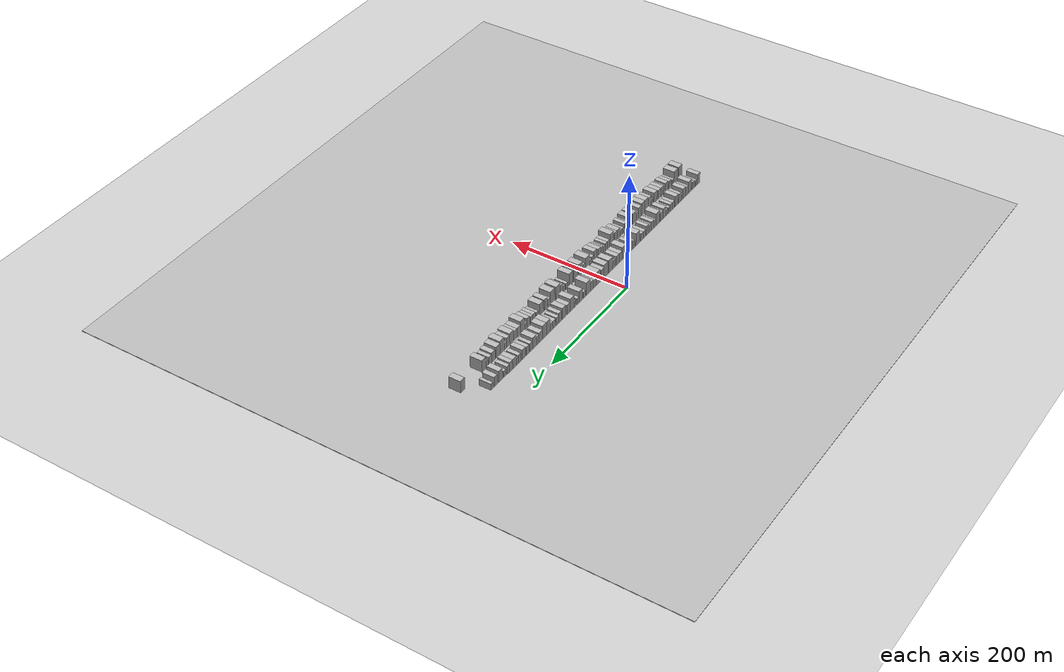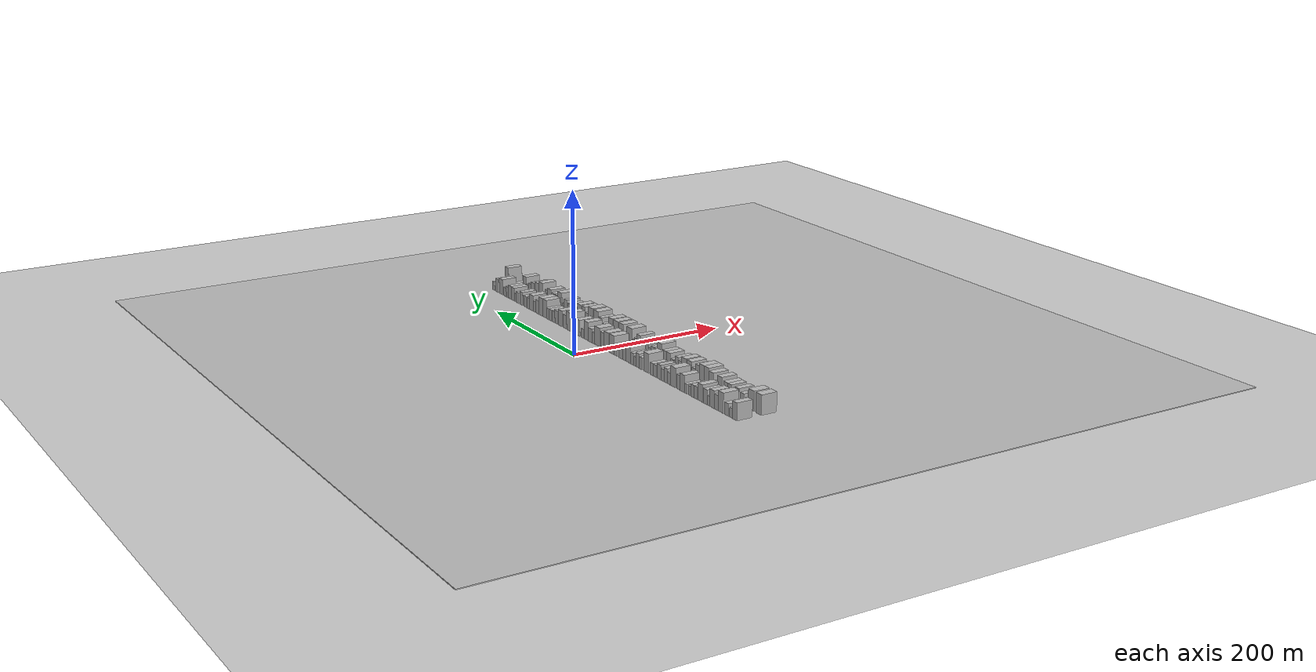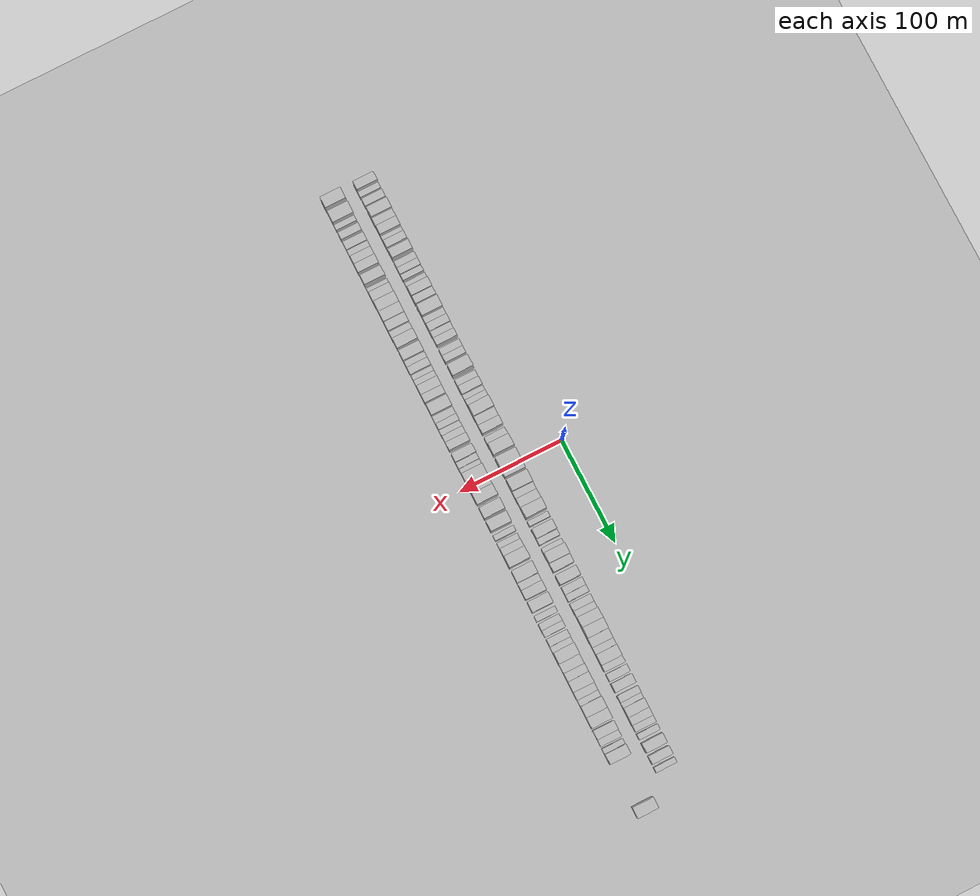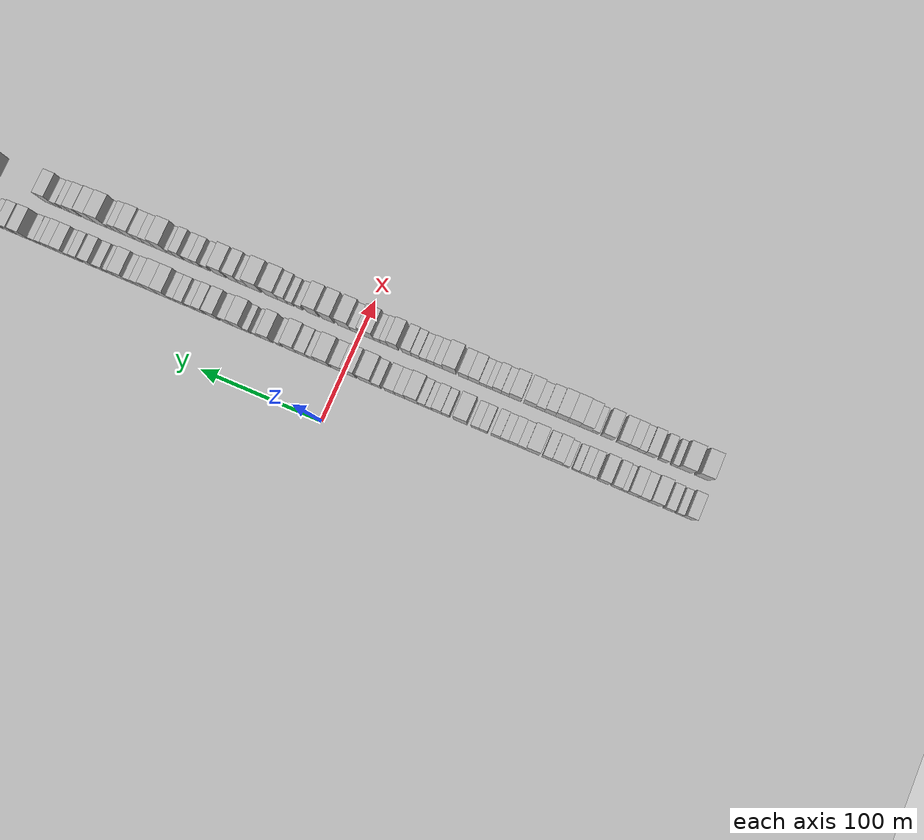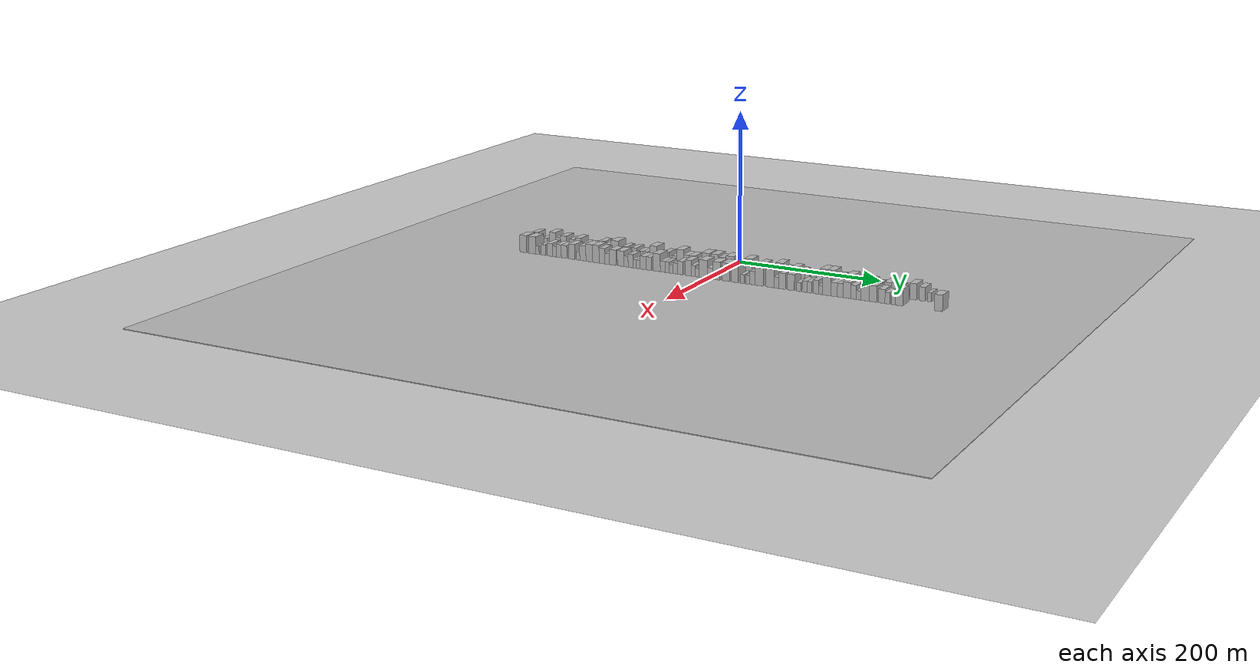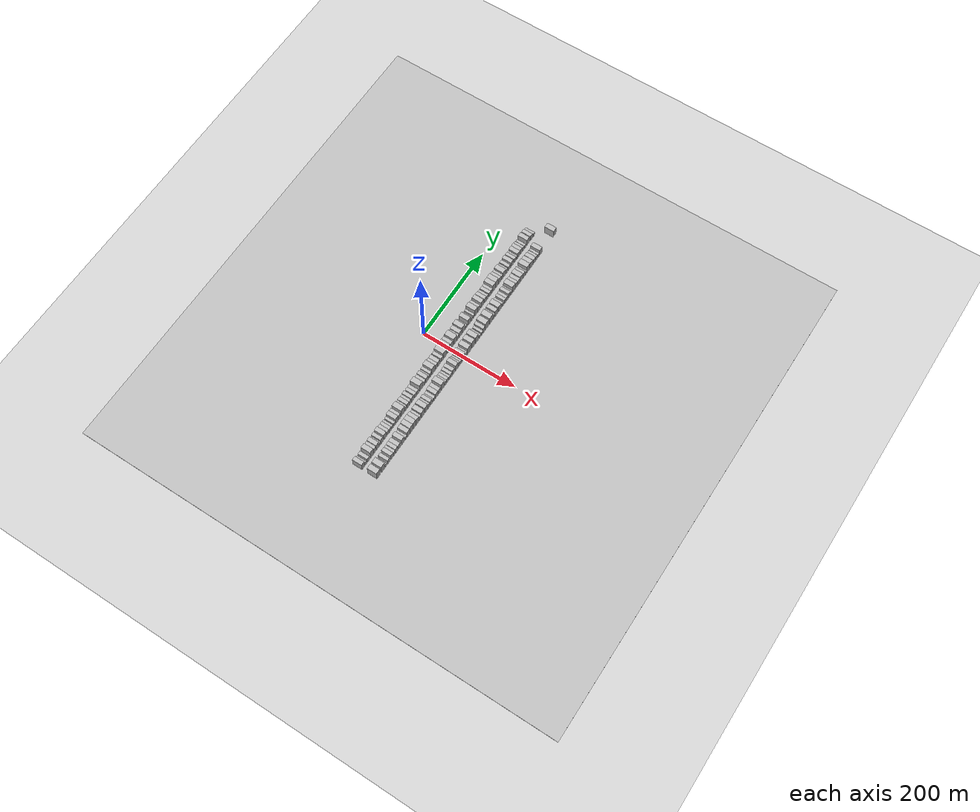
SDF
<?xml version="1.0" encoding="utf-8"?>

<sdf version="1.6">

   <world name="default">

      <gui fullscreen="0">

         <camera name="user_camera">

            <pose>-15 0 4.57585 0 0 0</pose>

            <view_controller>orbit</view_controller>

         </camera>

      </gui>

      <scene>

         <sky>

           <clouds>

             <speed>12</speed>

           </clouds>

         </sky>

         <ambient>0.4 0.4 0.4 1</ambient>

         <background>0.7 0.7 0.7 1</background>

         <shadows>1</shadows>

      </scene>

      <gravity>0 0 -9.8066</gravity>

      <magnetic_field>6e-06 2.3e-05 -4.2e-05</magnetic_field>

      <physics default="0" name="default_physics" type="ode">

         <ode>

            <solver>

               <type>quick</type>

               <iters>10</iters>

               <sor>1.0</sor>

               <use_dynamic_moi_rescaling>0</use_dynamic_moi_rescaling>

            </solver>

            <constraints>

               <cfm>0</cfm>

               <erp>0.2</erp>

               <contact_max_correcting_vel>100</contact_max_correcting_vel>

               <contact_surface_layer>0.001</contact_surface_layer>

            </constraints>

         </ode>

         <max_step_size>0.004</max_step_size>

         <real_time_factor>1</real_time_factor>

         <real_time_update_rate>250</real_time_update_rate>

      </physics>

      <light name="sun" type="directional">

         <cast_shadows>1</cast_shadows>

         <pose>0 0 10 0 0 0</pose>

         <diffuse>0.8 0.8 0.8 1</diffuse>

         <specular>0.2 0.2 0.2 1</specular>

         <attenuation>

            <range>1000</range>

            <constant>0.9</constant>

            <linear>0.01</linear>

            <quadratic>0.001</quadratic>

         </attenuation>

         <direction>-0.5 0.1 -0.9</direction>

      </light>

      <include>

         <name>ground_plane_1</name>

         <uri>model://HANNAS_ground_plane</uri>

         <pose>0 0 0  0 0 0</pose>

      </include>

      <include>

         <name>ground_plane_2</name>

         <uri>model://HANNAS_ground_plane</uri>

         <pose>100 0 0  0 0 0</pose>

      </include>

      <model name="building_1">

         <static>1</static>

         <pose frame="">50.0000 -279.7703 0 0.000000 0.000000 0.000000</pose>

         <link name="link">

            <pose frame="">0 0 10.50 0 0 0</pose>

            <collision name="collision">

               <geometry>

                  <box>

                     <size>20.0000 8.4593 21.0000</size>

                  </box>

               </geometry>

               <max_contacts>10</max_contacts>

               <surface>

                  <contact>

                     <ode/>

                  </contact>

                  <bounce/>

                  <friction>

                     <torsional>

                        <ode/>

                     </torsional>

                     <ode/>

                  </friction>

               </surface>

            </collision>

            <visual name="visual">

               <cast_shadows>0</cast_shadows>

               <geometry>

                  <box>

                     <size>20.0000 8.4593 21.0000</size>

                  </box>

               </geometry>

               <material>

                  <script>

                     <uri>model://HANNAS_wall/materials/scripts</uri>

                     <uri>model://HANNAS_wall/materials/textures</uri>

                     <name>vrc/HANNAS_wall</name>

                  </script>

               </material>

            </visual>

            <self_collide>0</self_collide>

            <enable_wind>0</enable_wind>

            <kinematic>0</kinematic>

         </link>

      </model>

      <model name="building_2">

         <static>1</static>

         <pose frame="">50.0000 -272.6795 0 0.000000 0.000000 0.000000</pose>

         <link name="link">

            <pose frame="">0 0 6.00 0 0 0</pose>

            <collision name="collision">

               <geometry>

                  <box>

                     <size>20.0000 5.7224 12.0000</size>

                  </box>

               </geometry>

               <max_contacts>10</max_contacts>

               <surface>

                  <contact>

                     <ode/>

                  </contact>

                  <bounce/>

                  <friction>

                     <torsional>

                        <ode/>

                     </torsional>

                     <ode/>

                  </friction>

               </surface>

            </collision>

            <visual name="visual">

               <cast_shadows>0</cast_shadows>

               <geometry>

                  <box>

                     <size>20.0000 5.7224 12.0000</size>

                  </box>

               </geometry>

               <material>

                  <script>

                     <uri>model://HANNAS_wall/materials/scripts</uri>

                     <uri>model://HANNAS_wall/materials/textures</uri>

                     <name>vrc/HANNAS_wall</name>

                  </script>

               </material>

            </visual>

            <self_collide>0</self_collide>

            <enable_wind>0</enable_wind>

            <kinematic>0</kinematic>

         </link>

      </model>

      <model name="building_3">

         <static>1</static>

         <pose frame="">50.0000 -264.1542 0 0.000000 0.000000 0.000000</pose>

         <link name="link">

            <pose frame="">0 0 7.50 0 0 0</pose>

            <collision name="collision">

               <geometry>

                  <box>

                     <size>20.0000 7.3282 15.0000</size>

                  </box>

               </geometry>

               <max_contacts>10</max_contacts>

               <surface>

                  <contact>

                     <ode/>

                  </contact>

                  <bounce/>

                  <friction>

                     <torsional>

                        <ode/>

                     </torsional>

                     <ode/>

                  </friction>

               </surface>

            </collision>

            <visual name="visual">

               <cast_shadows>0</cast_shadows>

               <geometry>

                  <box>

                     <size>20.0000 7.3282 15.0000</size>

                  </box>

               </geometry>

               <material>

                  <script>

                     <uri>model://HANNAS_wall/materials/scripts</uri>

                     <uri>model://HANNAS_wall/materials/textures</uri>

                     <name>vrc/HANNAS_wall</name>

                  </script>

               </material>

            </visual>

            <self_collide>0</self_collide>

            <enable_wind>0</enable_wind>

            <kinematic>0</kinematic>

         </link>

      </model>

      <model name="building_4">

         <static>1</static>

         <pose frame="">50.0000 -252.5443 0 0.000000 0.000000 0.000000</pose>

         <link name="link">

            <pose frame="">0 0 12.00 0 0 0</pose>

            <collision name="collision">

               <geometry>

                  <box>

                     <size>20.0000 9.8916 24.0000</size>

                  </box>

               </geometry>

               <max_contacts>10</max_contacts>

               <surface>

                  <contact>

                     <ode/>

                  </contact>

                  <bounce/>

                  <friction>

                     <torsional>

                        <ode/>

                     </torsional>

                     <ode/>

                  </friction>

               </surface>

            </collision>

            <visual name="visual">

               <cast_shadows>0</cast_shadows>

               <geometry>

                  <box>

                     <size>20.0000 9.8916 24.0000</size>

                  </box>

               </geometry>

               <material>

                  <script>

                     <uri>model://HANNAS_wall/materials/scripts</uri>

                     <uri>model://HANNAS_wall/materials/textures</uri>

                     <name>vrc/HANNAS_wall</name>

                  </script>

               </material>

            </visual>

            <self_collide>0</self_collide>

            <enable_wind>0</enable_wind>

            <kinematic>0</kinematic>

         </link>

      </model>

      <model name="building_5">

         <static>1</static>

         <pose frame="">50.0000 -243.5871 0 0.000000 0.000000 0.000000</pose>

         <link name="link">

            <pose frame="">0 0 9.00 0 0 0</pose>

            <collision name="collision">

               <geometry>

                  <box>

                     <size>20.0000 8.0228 18.0000</size>

                  </box>

               </geometry>

               <max_contacts>10</max_contacts>

               <surface>

                  <contact>

                     <ode/>

                  </contact>

                  <bounce/>

                  <friction>

                     <torsional>

                        <ode/>

                     </torsional>

                     <ode/>

                  </friction>

               </surface>

            </collision>

            <visual name="visual">

               <cast_shadows>0</cast_shadows>

               <geometry>

                  <box>

                     <size>20.0000 8.0228 18.0000</size>

                  </box>

               </geometry>

               <material>

                  <script>

                     <uri>model://HANNAS_wall/materials/scripts</uri>

                     <uri>model://HANNAS_wall/materials/textures</uri>

                     <name>vrc/HANNAS_wall</name>

                  </script>

               </material>

            </visual>

            <self_collide>0</self_collide>

            <enable_wind>0</enable_wind>

            <kinematic>0</kinematic>

         </link>

      </model>

      <model name="building_6">

         <static>1</static>

         <pose frame="">50.0000 -235.2132 0 0.000000 0.000000 0.000000</pose>

         <link name="link">

            <pose frame="">0 0 10.50 0 0 0</pose>

            <collision name="collision">

               <geometry>

                  <box>

                     <size>20.0000 8.7249 21.0000</size>

                  </box>

               </geometry>

               <max_contacts>10</max_contacts>

               <surface>

                  <contact>

                     <ode/>

                  </contact>

                  <bounce/>

                  <friction>

                     <torsional>

                        <ode/>

                     </torsional>

                     <ode/>

                  </friction>

               </surface>

            </collision>

            <visual name="visual">

               <cast_shadows>0</cast_shadows>

               <geometry>

                  <box>

                     <size>20.0000 8.7249 21.0000</size>

                  </box>

               </geometry>

               <material>

                  <script>

                     <uri>model://HANNAS_wall/materials/scripts</uri>

                     <uri>model://HANNAS_wall/materials/textures</uri>

                     <name>vrc/HANNAS_wall</name>

                  </script>

               </material>

            </visual>

            <self_collide>0</self_collide>

            <enable_wind>0</enable_wind>

            <kinematic>0</kinematic>

         </link>

      </model>

      <model name="building_7">

         <static>1</static>

         <pose frame="">50.0000 -228.3321 0 0.000000 0.000000 0.000000</pose>

         <link name="link">

            <pose frame="">0 0 6.00 0 0 0</pose>

            <collision name="collision">

               <geometry>

                  <box>

                     <size>20.0000 5.0373 12.0000</size>

                  </box>

               </geometry>

               <max_contacts>10</max_contacts>

               <surface>

                  <contact>

                     <ode/>

                  </contact>

                  <bounce/>

                  <friction>

                     <torsional>

                        <ode/>

                     </torsional>

                     <ode/>

                  </friction>

               </surface>

            </collision>

            <visual name="visual">

               <cast_shadows>0</cast_shadows>

               <geometry>

                  <box>

                     <size>20.0000 5.0373 12.0000</size>

                  </box>

               </geometry>

               <material>

                  <script>

                     <uri>model://HANNAS_wall/materials/scripts</uri>

                     <uri>model://HANNAS_wall/materials/textures</uri>

                     <name>vrc/HANNAS_wall</name>

                  </script>

               </material>

            </visual>

            <self_collide>0</self_collide>

            <enable_wind>0</enable_wind>

            <kinematic>0</kinematic>

         </link>

      </model>

      <model name="building_8">

         <static>1</static>

         <pose frame="">50.0000 -222.1160 0 0.000000 0.000000 0.000000</pose>

         <link name="link">

            <pose frame="">0 0 9.00 0 0 0</pose>

            <collision name="collision">

               <geometry>

                  <box>

                     <size>20.0000 7.3950 18.0000</size>

                  </box>

               </geometry>

               <max_contacts>10</max_contacts>

               <surface>

                  <contact>

                     <ode/>

                  </contact>

                  <bounce/>

                  <friction>

                     <torsional>

                        <ode/>

                     </torsional>

                     <ode/>

                  </friction>

               </surface>

            </collision>

            <visual name="visual">

               <cast_shadows>0</cast_shadows>

               <geometry>

                  <box>

                     <size>20.0000 7.3950 18.0000</size>

                  </box>

               </geometry>

               <material>

                  <script>

                     <uri>model://HANNAS_wall/materials/scripts</uri>

                     <uri>model://HANNAS_wall/materials/textures</uri>

                     <name>vrc/HANNAS_wall</name>

                  </script>

               </material>

            </visual>

            <self_collide>0</self_collide>

            <enable_wind>0</enable_wind>

            <kinematic>0</kinematic>

         </link>

      </model>

      <model name="building_9">

         <static>1</static>

         <pose frame="">50.0000 -211.9056 0 0.000000 0.000000 0.000000</pose>

         <link name="link">

            <pose frame="">0 0 10.50 0 0 0</pose>

            <collision name="collision">

               <geometry>

                  <box>

                     <size>20.0000 9.0258 21.0000</size>

                  </box>

               </geometry>

               <max_contacts>10</max_contacts>

               <surface>

                  <contact>

                     <ode/>

                  </contact>

                  <bounce/>

                  <friction>

                     <torsional>

                        <ode/>

                     </torsional>

                     <ode/>

                  </friction>

               </surface>

            </collision>

            <visual name="visual">

               <cast_shadows>0</cast_shadows>

               <geometry>

                  <box>

                     <size>20.0000 9.0258 21.0000</size>

                  </box>

               </geometry>

               <material>

                  <script>

                     <uri>model://HANNAS_wall/materials/scripts</uri>

                     <uri>model://HANNAS_wall/materials/textures</uri>

                     <name>vrc/HANNAS_wall</name>

                  </script>

               </material>

            </visual>

            <self_collide>0</self_collide>

            <enable_wind>0</enable_wind>

            <kinematic>0</kinematic>

         </link>

      </model>

      <model name="building_10">

         <static>1</static>

         <pose frame="">50.0000 -202.2077 0 0.000000 0.000000 0.000000</pose>

         <link name="link">

            <pose frame="">0 0 7.50 0 0 0</pose>

            <collision name="collision">

               <geometry>

                  <box>

                     <size>20.0000 6.3702 15.0000</size>

                  </box>

               </geometry>

               <max_contacts>10</max_contacts>

               <surface>

                  <contact>

                     <ode/>

                  </contact>

                  <bounce/>

                  <friction>

                     <torsional>

                        <ode/>

                     </torsional>

                     <ode/>

                  </friction>

               </surface>

            </collision>

            <visual name="visual">

               <cast_shadows>0</cast_shadows>

               <geometry>

                  <box>

                     <size>20.0000 6.3702 15.0000</size>

                  </box>

               </geometry>

               <material>

                  <script>

                     <uri>model://HANNAS_wall/materials/scripts</uri>

                     <uri>model://HANNAS_wall/materials/textures</uri>

                     <name>vrc/HANNAS_wall</name>

                  </script>

               </material>

            </visual>

            <self_collide>0</self_collide>

            <enable_wind>0</enable_wind>

            <kinematic>0</kinematic>

         </link>

      </model>

      <model name="building_11">

         <static>1</static>

         <pose frame="">50.0000 -195.7344 0 0.000000 0.000000 0.000000</pose>

         <link name="link">

            <pose frame="">0 0 7.50 0 0 0</pose>

            <collision name="collision">

               <geometry>

                  <box>

                     <size>20.0000 6.5764 15.0000</size>

                  </box>

               </geometry>

               <max_contacts>10</max_contacts>

               <surface>

                  <contact>

                     <ode/>

                  </contact>

                  <bounce/>

                  <friction>

                     <torsional>

                        <ode/>

                     </torsional>

                     <ode/>

                  </friction>

               </surface>

            </collision>

            <visual name="visual">

               <cast_shadows>0</cast_shadows>

               <geometry>

                  <box>

                     <size>20.0000 6.5764 15.0000</size>

                  </box>

               </geometry>

               <material>

                  <script>

                     <uri>model://HANNAS_wall/materials/scripts</uri>

                     <uri>model://HANNAS_wall/materials/textures</uri>

                     <name>vrc/HANNAS_wall</name>

                  </script>

               </material>

            </visual>

            <self_collide>0</self_collide>

            <enable_wind>0</enable_wind>

            <kinematic>0</kinematic>

         </link>

      </model>

      <model name="building_12">

         <static>1</static>

         <pose frame="">50.0000 -189.6909 0 0.000000 0.000000 0.000000</pose>

         <link name="link">

            <pose frame="">0 0 6.00 0 0 0</pose>

            <collision name="collision">

               <geometry>

                  <box>

                     <size>20.0000 5.5105 12.0000</size>

                  </box>

               </geometry>

               <max_contacts>10</max_contacts>

               <surface>

                  <contact>

                     <ode/>

                  </contact>

                  <bounce/>

                  <friction>

                     <torsional>

                        <ode/>

                     </torsional>

                     <ode/>

                  </friction>

               </surface>

            </collision>

            <visual name="visual">

               <cast_shadows>0</cast_shadows>

               <geometry>

                  <box>

                     <size>20.0000 5.5105 12.0000</size>

                  </box>

               </geometry>

               <material>

                  <script>

                     <uri>model://HANNAS_wall/materials/scripts</uri>

                     <uri>model://HANNAS_wall/materials/textures</uri>

                     <name>vrc/HANNAS_wall</name>

                  </script>

               </material>

            </visual>

            <self_collide>0</self_collide>

            <enable_wind>0</enable_wind>

            <kinematic>0</kinematic>

         </link>

      </model>

      <model name="building_13">

         <static>1</static>

         <pose frame="">50.0000 -182.0485 0 0.000000 0.000000 0.000000</pose>

         <link name="link">

            <pose frame="">0 0 6.00 0 0 0</pose>

            <collision name="collision">

               <geometry>

                  <box>

                     <size>20.0000 5.7744 12.0000</size>

                  </box>

               </geometry>

               <max_contacts>10</max_contacts>

               <surface>

                  <contact>

                     <ode/>

                  </contact>

                  <bounce/>

                  <friction>

                     <torsional>

                        <ode/>

                     </torsional>

                     <ode/>

                  </friction>

               </surface>

            </collision>

            <visual name="visual">

               <cast_shadows>0</cast_shadows>

               <geometry>

                  <box>

                     <size>20.0000 5.7744 12.0000</size>

                  </box>

               </geometry>

               <material>

                  <script>

                     <uri>model://HANNAS_wall/materials/scripts</uri>

                     <uri>model://HANNAS_wall/materials/textures</uri>

                     <name>vrc/HANNAS_wall</name>

                  </script>

               </material>

            </visual>

            <self_collide>0</self_collide>

            <enable_wind>0</enable_wind>

            <kinematic>0</kinematic>

         </link>

      </model>

      <model name="building_14">

         <static>1</static>

         <pose frame="">50.0000 -174.7064 0 0.000000 0.000000 0.000000</pose>

         <link name="link">

            <pose frame="">0 0 10.50 0 0 0</pose>

            <collision name="collision">

               <geometry>

                  <box>

                     <size>20.0000 8.9098 21.0000</size>

                  </box>

               </geometry>

               <max_contacts>10</max_contacts>

               <surface>

                  <contact>

                     <ode/>

                  </contact>

                  <bounce/>

                  <friction>

                     <torsional>

                        <ode/>

                     </torsional>

                     <ode/>

                  </friction>

               </surface>

            </collision>

            <visual name="visual">

               <cast_shadows>0</cast_shadows>

               <geometry>

                  <box>

                     <size>20.0000 8.9098 21.0000</size>

                  </box>

               </geometry>

               <material>

                  <script>

                     <uri>model://HANNAS_wall/materials/scripts</uri>

                     <uri>model://HANNAS_wall/materials/textures</uri>

                     <name>vrc/HANNAS_wall</name>

                  </script>

               </material>

            </visual>

            <self_collide>0</self_collide>

            <enable_wind>0</enable_wind>

            <kinematic>0</kinematic>

         </link>

      </model>

      <model name="building_15">

         <static>1</static>

         <pose frame="">50.0000 -166.5727 0 0.000000 0.000000 0.000000</pose>

         <link name="link">

            <pose frame="">0 0 9.00 0 0 0</pose>

            <collision name="collision">

               <geometry>

                  <box>

                     <size>20.0000 7.3575 18.0000</size>

                  </box>

               </geometry>

               <max_contacts>10</max_contacts>

               <surface>

                  <contact>

                     <ode/>

                  </contact>

                  <bounce/>

                  <friction>

                     <torsional>

                        <ode/>

                     </torsional>

                     <ode/>

                  </friction>

               </surface>

            </collision>

            <visual name="visual">

               <cast_shadows>0</cast_shadows>

               <geometry>

                  <box>

                     <size>20.0000 7.3575 18.0000</size>

                  </box>

               </geometry>

               <material>

                  <script>

                     <uri>model://HANNAS_wall/materials/scripts</uri>

                     <uri>model://HANNAS_wall/materials/textures</uri>

                     <name>vrc/HANNAS_wall</name>

                  </script>

               </material>

            </visual>

            <self_collide>0</self_collide>

            <enable_wind>0</enable_wind>

            <kinematic>0</kinematic>

         </link>

      </model>

      <model name="building_16">

         <static>1</static>

         <pose frame="">50.0000 -155.3048 0 0.000000 0.000000 0.000000</pose>

         <link name="link">

            <pose frame="">0 0 12.00 0 0 0</pose>

            <collision name="collision">

               <geometry>

                  <box>

                     <size>20.0000 11.1784 24.0000</size>

                  </box>

               </geometry>

               <max_contacts>10</max_contacts>

               <surface>

                  <contact>

                     <ode/>

                  </contact>

                  <bounce/>

                  <friction>

                     <torsional>

                        <ode/>

                     </torsional>

                     <ode/>

                  </friction>

               </surface>

            </collision>

            <visual name="visual">

               <cast_shadows>0</cast_shadows>

               <geometry>

                  <box>

                     <size>20.0000 11.1784 24.0000</size>

                  </box>

               </geometry>

               <material>

                  <script>

                     <uri>model://HANNAS_wall/materials/scripts</uri>

                     <uri>model://HANNAS_wall/materials/textures</uri>

                     <name>vrc/HANNAS_wall</name>

                  </script>

               </material>

            </visual>

            <self_collide>0</self_collide>

            <enable_wind>0</enable_wind>

            <kinematic>0</kinematic>

         </link>

      </model>

      <model name="building_17">

         <static>1</static>

         <pose frame="">50.0000 -146.4196 0 0.000000 0.000000 0.000000</pose>

         <link name="link">

            <pose frame="">0 0 7.50 0 0 0</pose>

            <collision name="collision">

               <geometry>

                  <box>

                     <size>20.0000 6.5921 15.0000</size>

                  </box>

               </geometry>

               <max_contacts>10</max_contacts>

               <surface>

                  <contact>

                     <ode/>

                  </contact>

                  <bounce/>

                  <friction>

                     <torsional>

                        <ode/>

                     </torsional>

                     <ode/>

                  </friction>

               </surface>

            </collision>

            <visual name="visual">

               <cast_shadows>0</cast_shadows>

               <geometry>

                  <box>

                     <size>20.0000 6.5921 15.0000</size>

                  </box>

               </geometry>

               <material>

                  <script>

                     <uri>model://HANNAS_wall/materials/scripts</uri>

                     <uri>model://HANNAS_wall/materials/textures</uri>

                     <name>vrc/HANNAS_wall</name>

                  </script>

               </material>

            </visual>

            <self_collide>0</self_collide>

            <enable_wind>0</enable_wind>

            <kinematic>0</kinematic>

         </link>

      </model>

      <model name="building_18">

         <static>1</static>

         <pose frame="">50.0000 -139.3675 0 0.000000 0.000000 0.000000</pose>

         <link name="link">

            <pose frame="">0 0 9.00 0 0 0</pose>

            <collision name="collision">

               <geometry>

                  <box>

                     <size>20.0000 7.5121 18.0000</size>

                  </box>

               </geometry>

               <max_contacts>10</max_contacts>

               <surface>

                  <contact>

                     <ode/>

                  </contact>

                  <bounce/>

                  <friction>

                     <torsional>

                        <ode/>

                     </torsional>

                     <ode/>

                  </friction>

               </surface>

            </collision>

            <visual name="visual">

               <cast_shadows>0</cast_shadows>

               <geometry>

                  <box>

                     <size>20.0000 7.5121 18.0000</size>

                  </box>

               </geometry>

               <material>

                  <script>

                     <uri>model://HANNAS_wall/materials/scripts</uri>

                     <uri>model://HANNAS_wall/materials/textures</uri>

                     <name>vrc/HANNAS_wall</name>

                  </script>

               </material>

            </visual>

            <self_collide>0</self_collide>

            <enable_wind>0</enable_wind>

            <kinematic>0</kinematic>

         </link>

      </model>

      <model name="building_19">

         <static>1</static>

         <pose frame="">50.0000 -132.3308 0 0.000000 0.000000 0.000000</pose>

         <link name="link">

            <pose frame="">0 0 7.50 0 0 0</pose>

            <collision name="collision">

               <geometry>

                  <box>

                     <size>20.0000 6.5614 15.0000</size>

                  </box>

               </geometry>

               <max_contacts>10</max_contacts>

               <surface>

                  <contact>

                     <ode/>

                  </contact>

                  <bounce/>

                  <friction>

                     <torsional>

                        <ode/>

                     </torsional>

                     <ode/>

                  </friction>

               </surface>

            </collision>

            <visual name="visual">

               <cast_shadows>0</cast_shadows>

               <geometry>

                  <box>

                     <size>20.0000 6.5614 15.0000</size>

                  </box>

               </geometry>

               <material>

                  <script>

                     <uri>model://HANNAS_wall/materials/scripts</uri>

                     <uri>model://HANNAS_wall/materials/textures</uri>

                     <name>vrc/HANNAS_wall</name>

                  </script>

               </material>

            </visual>

            <self_collide>0</self_collide>

            <enable_wind>0</enable_wind>

            <kinematic>0</kinematic>

         </link>

      </model>

      <model name="building_20">

         <static>1</static>

         <pose frame="">50.0000 -125.4148 0 0.000000 0.000000 0.000000</pose>

         <link name="link">

            <pose frame="">0 0 9.00 0 0 0</pose>

            <collision name="collision">

               <geometry>

                  <box>

                     <size>20.0000 7.2706 18.0000</size>

                  </box>

               </geometry>

               <max_contacts>10</max_contacts>

               <surface>

                  <contact>

                     <ode/>

                  </contact>

                  <bounce/>

                  <friction>

                     <torsional>

                        <ode/>

                     </torsional>

                     <ode/>

                  </friction>

               </surface>

            </collision>

            <visual name="visual">

               <cast_shadows>0</cast_shadows>

               <geometry>

                  <box>

                     <size>20.0000 7.2706 18.0000</size>

                  </box>

               </geometry>

               <material>

                  <script>

                     <uri>model://HANNAS_wall/materials/scripts</uri>

                     <uri>model://HANNAS_wall/materials/textures</uri>

                     <name>vrc/HANNAS_wall</name>

                  </script>

               </material>

            </visual>

            <self_collide>0</self_collide>

            <enable_wind>0</enable_wind>

            <kinematic>0</kinematic>

         </link>

      </model>

      <model name="building_21">

         <static>1</static>

         <pose frame="">50.0000 -115.3287 0 0.000000 0.000000 0.000000</pose>

         <link name="link">

            <pose frame="">0 0 7.50 0 0 0</pose>

            <collision name="collision">

               <geometry>

                  <box>

                     <size>20.0000 6.9017 15.0000</size>

                  </box>

               </geometry>

               <max_contacts>10</max_contacts>

               <surface>

                  <contact>

                     <ode/>

                  </contact>

                  <bounce/>

                  <friction>

                     <torsional>

                        <ode/>

                     </torsional>

                     <ode/>

                  </friction>

               </surface>

            </collision>

            <visual name="visual">

               <cast_shadows>0</cast_shadows>

               <geometry>

                  <box>

                     <size>20.0000 6.9017 15.0000</size>

                  </box>

               </geometry>

               <material>

                  <script>

                     <uri>model://HANNAS_wall/materials/scripts</uri>

                     <uri>model://HANNAS_wall/materials/textures</uri>

                     <name>vrc/HANNAS_wall</name>

                  </script>

               </material>

            </visual>

            <self_collide>0</self_collide>

            <enable_wind>0</enable_wind>

            <kinematic>0</kinematic>

         </link>

      </model>

      <model name="building_22">

         <static>1</static>

         <pose frame="">50.0000 -108.5586 0 0.000000 0.000000 0.000000</pose>

         <link name="link">

            <pose frame="">0 0 7.50 0 0 0</pose>

            <collision name="collision">

               <geometry>

                  <box>

                     <size>20.0000 6.6385 15.0000</size>

                  </box>

               </geometry>

               <max_contacts>10</max_contacts>

               <surface>

                  <contact>

                     <ode/>

                  </contact>

                  <bounce/>

                  <friction>

                     <torsional>

                        <ode/>

                     </torsional>

                     <ode/>

                  </friction>

               </surface>

            </collision>

            <visual name="visual">

               <cast_shadows>0</cast_shadows>

               <geometry>

                  <box>

                     <size>20.0000 6.6385 15.0000</size>

                  </box>

               </geometry>

               <material>

                  <script>

                     <uri>model://HANNAS_wall/materials/scripts</uri>

                     <uri>model://HANNAS_wall/materials/textures</uri>

                     <name>vrc/HANNAS_wall</name>

                  </script>

               </material>

            </visual>

            <self_collide>0</self_collide>

            <enable_wind>0</enable_wind>

            <kinematic>0</kinematic>

         </link>

      </model>

      <model name="building_23">

         <static>1</static>

         <pose frame="">50.0000 -96.6324 0 0.000000 0.000000 0.000000</pose>

         <link name="link">

            <pose frame="">0 0 12.00 0 0 0</pose>

            <collision name="collision">

               <geometry>

                  <box>

                     <size>20.0000 11.2139 24.0000</size>

                  </box>

               </geometry>

               <max_contacts>10</max_contacts>

               <surface>

                  <contact>

                     <ode/>

                  </contact>

                  <bounce/>

                  <friction>

                     <torsional>

                        <ode/>

                     </torsional>

                     <ode/>

                  </friction>

               </surface>

            </collision>

            <visual name="visual">

               <cast_shadows>0</cast_shadows>

               <geometry>

                  <box>

                     <size>20.0000 11.2139 24.0000</size>

                  </box>

               </geometry>

               <material>

                  <script>

                     <uri>model://HANNAS_wall/materials/scripts</uri>

                     <uri>model://HANNAS_wall/materials/textures</uri>

                     <name>vrc/HANNAS_wall</name>

                  </script>

               </material>

            </visual>

            <self_collide>0</self_collide>

            <enable_wind>0</enable_wind>

            <kinematic>0</kinematic>

         </link>

      </model>

      <model name="building_24">

         <static>1</static>

         <pose frame="">50.0000 -84.7754 0 0.000000 0.000000 0.000000</pose>

         <link name="link">

            <pose frame="">0 0 7.50 0 0 0</pose>

            <collision name="collision">

               <geometry>

                  <box>

                     <size>20.0000 6.5001 15.0000</size>

                  </box>

               </geometry>

               <max_contacts>10</max_contacts>

               <surface>

                  <contact>

                     <ode/>

                  </contact>

                  <bounce/>

                  <friction>

                     <torsional>

                        <ode/>

                     </torsional>

                     <ode/>

                  </friction>

               </surface>

            </collision>

            <visual name="visual">

               <cast_shadows>0</cast_shadows>

               <geometry>

                  <box>

                     <size>20.0000 6.5001 15.0000</size>

                  </box>

               </geometry>

               <material>

                  <script>

                     <uri>model://HANNAS_wall/materials/scripts</uri>

                     <uri>model://HANNAS_wall/materials/textures</uri>

                     <name>vrc/HANNAS_wall</name>

                  </script>

               </material>

            </visual>

            <self_collide>0</self_collide>

            <enable_wind>0</enable_wind>

            <kinematic>0</kinematic>

         </link>

      </model>

      <model name="building_25">

         <static>1</static>

         <pose frame="">50.0000 -77.5405 0 0.000000 0.000000 0.000000</pose>

         <link name="link">

            <pose frame="">0 0 9.00 0 0 0</pose>

            <collision name="collision">

               <geometry>

                  <box>

                     <size>20.0000 7.9698 18.0000</size>

                  </box>

               </geometry>

               <max_contacts>10</max_contacts>

               <surface>

                  <contact>

                     <ode/>

                  </contact>

                  <bounce/>

                  <friction>

                     <torsional>

                        <ode/>

                     </torsional>

                     <ode/>

                  </friction>

               </surface>

            </collision>

            <visual name="visual">

               <cast_shadows>0</cast_shadows>

               <geometry>

                  <box>

                     <size>20.0000 7.9698 18.0000</size>

                  </box>

               </geometry>

               <material>

                  <script>

                     <uri>model://HANNAS_wall/materials/scripts</uri>

                     <uri>model://HANNAS_wall/materials/textures</uri>

                     <name>vrc/HANNAS_wall</name>

                  </script>

               </material>

            </visual>

            <self_collide>0</self_collide>

            <enable_wind>0</enable_wind>

            <kinematic>0</kinematic>

         </link>

      </model>

      <model name="building_26">

         <static>1</static>

         <pose frame="">50.0000 -70.9993 0 0.000000 0.000000 0.000000</pose>

         <link name="link">

            <pose frame="">0 0 6.00 0 0 0</pose>

            <collision name="collision">

               <geometry>

                  <box>

                     <size>20.0000 5.1126 12.0000</size>

                  </box>

               </geometry>

               <max_contacts>10</max_contacts>

               <surface>

                  <contact>

                     <ode/>

                  </contact>

                  <bounce/>

                  <friction>

                     <torsional>

                        <ode/>

                     </torsional>

                     <ode/>

                  </friction>

               </surface>

            </collision>

            <visual name="visual">

               <cast_shadows>0</cast_shadows>

               <geometry>

                  <box>

                     <size>20.0000 5.1126 12.0000</size>

                  </box>

               </geometry>

               <material>

                  <script>

                     <uri>model://HANNAS_wall/materials/scripts</uri>

                     <uri>model://HANNAS_wall/materials/textures</uri>

                     <name>vrc/HANNAS_wall</name>

                  </script>

               </material>

            </visual>

            <self_collide>0</self_collide>

            <enable_wind>0</enable_wind>

            <kinematic>0</kinematic>

         </link>

      </model>

      <model name="building_27">

         <static>1</static>

         <pose frame="">50.0000 -65.3010 0 0.000000 0.000000 0.000000</pose>

         <link name="link">

            <pose frame="">0 0 7.50 0 0 0</pose>

            <collision name="collision">

               <geometry>

                  <box>

                     <size>20.0000 6.2841 15.0000</size>

                  </box>

               </geometry>

               <max_contacts>10</max_contacts>

               <surface>

                  <contact>

                     <ode/>

                  </contact>

                  <bounce/>

                  <friction>

                     <torsional>

                        <ode/>

                     </torsional>

                     <ode/>

                  </friction>

               </surface>

            </collision>

            <visual name="visual">

               <cast_shadows>0</cast_shadows>

               <geometry>

                  <box>

                     <size>20.0000 6.2841 15.0000</size>

                  </box>

               </geometry>

               <material>

                  <script>

                     <uri>model://HANNAS_wall/materials/scripts</uri>

                     <uri>model://HANNAS_wall/materials/textures</uri>

                     <name>vrc/HANNAS_wall</name>

                  </script>

               </material>

            </visual>

            <self_collide>0</self_collide>

            <enable_wind>0</enable_wind>

            <kinematic>0</kinematic>

         </link>

      </model>

      <model name="building_28">

         <static>1</static>

         <pose frame="">50.0000 -56.8508 0 0.000000 0.000000 0.000000</pose>

         <link name="link">

            <pose frame="">0 0 12.00 0 0 0</pose>

            <collision name="collision">

               <geometry>

                  <box>

                     <size>20.0000 10.6163 24.0000</size>

                  </box>

               </geometry>

               <max_contacts>10</max_contacts>

               <surface>

                  <contact>

                     <ode/>

                  </contact>

                  <bounce/>

                  <friction>

                     <torsional>

                        <ode/>

                     </torsional>

                     <ode/>

                  </friction>

               </surface>

            </collision>

            <visual name="visual">

               <cast_shadows>0</cast_shadows>

               <geometry>

                  <box>

                     <size>20.0000 10.6163 24.0000</size>

                  </box>

               </geometry>

               <material>

                  <script>

                     <uri>model://HANNAS_wall/materials/scripts</uri>

                     <uri>model://HANNAS_wall/materials/textures</uri>

                     <name>vrc/HANNAS_wall</name>

                  </script>

               </material>

            </visual>

            <self_collide>0</self_collide>

            <enable_wind>0</enable_wind>

            <kinematic>0</kinematic>

         </link>

      </model>

      <model name="building_29">

         <static>1</static>

         <pose frame="">50.0000 -47.4027 0 0.000000 0.000000 0.000000</pose>

         <link name="link">

            <pose frame="">0 0 9.00 0 0 0</pose>

            <collision name="collision">

               <geometry>

                  <box>

                     <size>20.0000 8.2799 18.0000</size>

                  </box>

               </geometry>

               <max_contacts>10</max_contacts>

               <surface>

                  <contact>

                     <ode/>

                  </contact>

                  <bounce/>

                  <friction>

                     <torsional>

                        <ode/>

                     </torsional>

                     <ode/>

                  </friction>

               </surface>

            </collision>

            <visual name="visual">

               <cast_shadows>0</cast_shadows>

               <geometry>

                  <box>

                     <size>20.0000 8.2799 18.0000</size>

                  </box>

               </geometry>

               <material>

                  <script>

                     <uri>model://HANNAS_wall/materials/scripts</uri>

                     <uri>model://HANNAS_wall/materials/textures</uri>

                     <name>vrc/HANNAS_wall</name>

                  </script>

               </material>

            </visual>

            <self_collide>0</self_collide>

            <enable_wind>0</enable_wind>

            <kinematic>0</kinematic>

         </link>

      </model>

      <model name="building_30">

         <static>1</static>

         <pose frame="">50.0000 -39.0832 0 0.000000 0.000000 0.000000</pose>

         <link name="link">

            <pose frame="">0 0 9.00 0 0 0</pose>

            <collision name="collision">

               <geometry>

                  <box>

                     <size>20.0000 8.3590 18.0000</size>

                  </box>

               </geometry>

               <max_contacts>10</max_contacts>

               <surface>

                  <contact>

                     <ode/>

                  </contact>

                  <bounce/>

                  <friction>

                     <torsional>

                        <ode/>

                     </torsional>

                     <ode/>

                  </friction>

               </surface>

            </collision>

            <visual name="visual">

               <cast_shadows>0</cast_shadows>

               <geometry>

                  <box>

                     <size>20.0000 8.3590 18.0000</size>

                  </box>

               </geometry>

               <material>

                  <script>

                     <uri>model://HANNAS_wall/materials/scripts</uri>

                     <uri>model://HANNAS_wall/materials/textures</uri>

                     <name>vrc/HANNAS_wall</name>

                  </script>

               </material>

            </visual>

            <self_collide>0</self_collide>

            <enable_wind>0</enable_wind>

            <kinematic>0</kinematic>

         </link>

      </model>

      <model name="building_31">

         <static>1</static>

         <pose frame="">50.0000 -28.3617 0 0.000000 0.000000 0.000000</pose>

         <link name="link">

            <pose frame="">0 0 7.50 0 0 0</pose>

            <collision name="collision">

               <geometry>

                  <box>

                     <size>20.0000 7.0841 15.0000</size>

                  </box>

               </geometry>

               <max_contacts>10</max_contacts>

               <surface>

                  <contact>

                     <ode/>

                  </contact>

                  <bounce/>

                  <friction>

                     <torsional>

                        <ode/>

                     </torsional>

                     <ode/>

                  </friction>

               </surface>

            </collision>

            <visual name="visual">

               <cast_shadows>0</cast_shadows>

               <geometry>

                  <box>

                     <size>20.0000 7.0841 15.0000</size>

                  </box>

               </geometry>

               <material>

                  <script>

                     <uri>model://HANNAS_wall/materials/scripts</uri>

                     <uri>model://HANNAS_wall/materials/textures</uri>

                     <name>vrc/HANNAS_wall</name>

                  </script>

               </material>

            </visual>

            <self_collide>0</self_collide>

            <enable_wind>0</enable_wind>

            <kinematic>0</kinematic>

         </link>

      </model>

      <model name="building_32">

         <static>1</static>

         <pose frame="">50.0000 -19.1570 0 0.000000 0.000000 0.000000</pose>

         <link name="link">

            <pose frame="">0 0 12.00 0 0 0</pose>

            <collision name="collision">

               <geometry>

                  <box>

                     <size>20.0000 11.3253 24.0000</size>

                  </box>

               </geometry>

               <max_contacts>10</max_contacts>

               <surface>

                  <contact>

                     <ode/>

                  </contact>

                  <bounce/>

                  <friction>

                     <torsional>

                        <ode/>

                     </torsional>

                     <ode/>

                  </friction>

               </surface>

            </collision>

            <visual name="visual">

               <cast_shadows>0</cast_shadows>

               <geometry>

                  <box>

                     <size>20.0000 11.3253 24.0000</size>

                  </box>

               </geometry>

               <material>

                  <script>

                     <uri>model://HANNAS_wall/materials/scripts</uri>

                     <uri>model://HANNAS_wall/materials/textures</uri>

                     <name>vrc/HANNAS_wall</name>

                  </script>

               </material>

            </visual>

            <self_collide>0</self_collide>

            <enable_wind>0</enable_wind>

            <kinematic>0</kinematic>

         </link>

      </model>

      <model name="building_33">

         <static>1</static>

         <pose frame="">50.0000 -6.0916 0 0.000000 0.000000 0.000000</pose>

         <link name="link">

            <pose frame="">0 0 12.00 0 0 0</pose>

            <collision name="collision">

               <geometry>

                  <box>

                     <size>20.0000 10.8056 24.0000</size>

                  </box>

               </geometry>

               <max_contacts>10</max_contacts>

               <surface>

                  <contact>

                     <ode/>

                  </contact>

                  <bounce/>

                  <friction>

                     <torsional>

                        <ode/>

                     </torsional>

                     <ode/>

                  </friction>

               </surface>

            </collision>

            <visual name="visual">

               <cast_shadows>0</cast_shadows>

               <geometry>

                  <box>

                     <size>20.0000 10.8056 24.0000</size>

                  </box>

               </geometry>

               <material>

                  <script>

                     <uri>model://HANNAS_wall/materials/scripts</uri>

                     <uri>model://HANNAS_wall/materials/textures</uri>

                     <name>vrc/HANNAS_wall</name>

                  </script>

               </material>

            </visual>

            <self_collide>0</self_collide>

            <enable_wind>0</enable_wind>

            <kinematic>0</kinematic>

         </link>

      </model>

      <model name="building_34">

         <static>1</static>

         <pose frame="">50.0000 3.6249 0 0.000000 0.000000 0.000000</pose>

         <link name="link">

            <pose frame="">0 0 10.50 0 0 0</pose>

            <collision name="collision">

               <geometry>

                  <box>

                     <size>20.0000 8.6273 21.0000</size>

                  </box>

               </geometry>

               <max_contacts>10</max_contacts>

               <surface>

                  <contact>

                     <ode/>

                  </contact>

                  <bounce/>

                  <friction>

                     <torsional>

                        <ode/>

                     </torsional>

                     <ode/>

                  </friction>

               </surface>

            </collision>

            <visual name="visual">

               <cast_shadows>0</cast_shadows>

               <geometry>

                  <box>

                     <size>20.0000 8.6273 21.0000</size>

                  </box>

               </geometry>

               <material>

                  <script>

                     <uri>model://HANNAS_wall/materials/scripts</uri>

                     <uri>model://HANNAS_wall/materials/textures</uri>

                     <name>vrc/HANNAS_wall</name>

                  </script>

               </material>

            </visual>

            <self_collide>0</self_collide>

            <enable_wind>0</enable_wind>

            <kinematic>0</kinematic>

         </link>

      </model>

      <model name="building_35">

         <static>1</static>

         <pose frame="">50.0000 15.7921 0 0.000000 0.000000 0.000000</pose>

         <link name="link">

            <pose frame="">0 0 12.00 0 0 0</pose>

            <collision name="collision">

               <geometry>

                  <box>

                     <size>20.0000 11.7071 24.0000</size>

                  </box>

               </geometry>

               <max_contacts>10</max_contacts>

               <surface>

                  <contact>

                     <ode/>

                  </contact>

                  <bounce/>

                  <friction>

                     <torsional>

                        <ode/>

                     </torsional>

                     <ode/>

                  </friction>

               </surface>

            </collision>

            <visual name="visual">

               <cast_shadows>0</cast_shadows>

               <geometry>

                  <box>

                     <size>20.0000 11.7071 24.0000</size>

                  </box>

               </geometry>

               <material>

                  <script>

                     <uri>model://HANNAS_wall/materials/scripts</uri>

                     <uri>model://HANNAS_wall/materials/textures</uri>

                     <name>vrc/HANNAS_wall</name>

                  </script>

               </material>

            </visual>

            <self_collide>0</self_collide>

            <enable_wind>0</enable_wind>

            <kinematic>0</kinematic>

         </link>

      </model>

      <model name="building_36">

         <static>1</static>

         <pose frame="">50.0000 25.0424 0 0.000000 0.000000 0.000000</pose>

         <link name="link">

            <pose frame="">0 0 7.50 0 0 0</pose>

            <collision name="collision">

               <geometry>

                  <box>

                     <size>20.0000 6.7934 15.0000</size>

                  </box>

               </geometry>

               <max_contacts>10</max_contacts>

               <surface>

                  <contact>

                     <ode/>

                  </contact>

                  <bounce/>

                  <friction>

                     <torsional>

                        <ode/>

                     </torsional>

                     <ode/>

                  </friction>

               </surface>

            </collision>

            <visual name="visual">

               <cast_shadows>0</cast_shadows>

               <geometry>

                  <box>

                     <size>20.0000 6.7934 15.0000</size>

                  </box>

               </geometry>

               <material>

                  <script>

                     <uri>model://HANNAS_wall/materials/scripts</uri>

                     <uri>model://HANNAS_wall/materials/textures</uri>

                     <name>vrc/HANNAS_wall</name>

                  </script>

               </material>

            </visual>

            <self_collide>0</self_collide>

            <enable_wind>0</enable_wind>

            <kinematic>0</kinematic>

         </link>

      </model>

      <model name="building_37">

         <static>1</static>

         <pose frame="">50.0000 32.8553 0 0.000000 0.000000 0.000000</pose>

         <link name="link">

            <pose frame="">0 0 9.00 0 0 0</pose>

            <collision name="collision">

               <geometry>

                  <box>

                     <size>20.0000 8.8324 18.0000</size>

                  </box>

               </geometry>

               <max_contacts>10</max_contacts>

               <surface>

                  <contact>

                     <ode/>

                  </contact>

                  <bounce/>

                  <friction>

                     <torsional>

                        <ode/>

                     </torsional>

                     <ode/>

                  </friction>

               </surface>

            </collision>

            <visual name="visual">

               <cast_shadows>0</cast_shadows>

               <geometry>

                  <box>

                     <size>20.0000 8.8324 18.0000</size>

                  </box>

               </geometry>

               <material>

                  <script>

                     <uri>model://HANNAS_wall/materials/scripts</uri>

                     <uri>model://HANNAS_wall/materials/textures</uri>

                     <name>vrc/HANNAS_wall</name>

                  </script>

               </material>

            </visual>

            <self_collide>0</self_collide>

            <enable_wind>0</enable_wind>

            <kinematic>0</kinematic>

         </link>

      </model>

      <model name="building_38">

         <static>1</static>

         <pose frame="">50.0000 42.4731 0 0.000000 0.000000 0.000000</pose>

         <link name="link">

            <pose frame="">0 0 12.00 0 0 0</pose>

            <collision name="collision">

               <geometry>

                  <box>

                     <size>20.0000 10.4032 24.0000</size>

                  </box>

               </geometry>

               <max_contacts>10</max_contacts>

               <surface>

                  <contact>

                     <ode/>

                  </contact>

                  <bounce/>

                  <friction>

                     <torsional>

                        <ode/>

                     </torsional>

                     <ode/>

                  </friction>

               </surface>

            </collision>

            <visual name="visual">

               <cast_shadows>0</cast_shadows>

               <geometry>

                  <box>

                     <size>20.0000 10.4032 24.0000</size>

                  </box>

               </geometry>

               <material>

                  <script>

                     <uri>model://HANNAS_wall/materials/scripts</uri>

                     <uri>model://HANNAS_wall/materials/textures</uri>

                     <name>vrc/HANNAS_wall</name>

                  </script>

               </material>

            </visual>

            <self_collide>0</self_collide>

            <enable_wind>0</enable_wind>

            <kinematic>0</kinematic>

         </link>

      </model>

      <model name="building_39">

         <static>1</static>

         <pose frame="">50.0000 52.2964 0 0.000000 0.000000 0.000000</pose>

         <link name="link">

            <pose frame="">0 0 6.00 0 0 0</pose>

            <collision name="collision">

               <geometry>

                  <box>

                     <size>20.0000 5.2434 12.0000</size>

                  </box>

               </geometry>

               <max_contacts>10</max_contacts>

               <surface>

                  <contact>

                     <ode/>

                  </contact>

                  <bounce/>

                  <friction>

                     <torsional>

                        <ode/>

                     </torsional>

                     <ode/>

                  </friction>

               </surface>

            </collision>

            <visual name="visual">

               <cast_shadows>0</cast_shadows>

               <geometry>

                  <box>

                     <size>20.0000 5.2434 12.0000</size>

                  </box>

               </geometry>

               <material>

                  <script>

                     <uri>model://HANNAS_wall/materials/scripts</uri>

                     <uri>model://HANNAS_wall/materials/textures</uri>

                     <name>vrc/HANNAS_wall</name>

                  </script>

               </material>

            </visual>

            <self_collide>0</self_collide>

            <enable_wind>0</enable_wind>

            <kinematic>0</kinematic>

         </link>

      </model>

      <model name="building_40">

         <static>1</static>

         <pose frame="">50.0000 62.6098 0 0.000000 0.000000 0.000000</pose>

         <link name="link">

            <pose frame="">0 0 10.50 0 0 0</pose>

            <collision name="collision">

               <geometry>

                  <box>

                     <size>20.0000 9.3833 21.0000</size>

                  </box>

               </geometry>

               <max_contacts>10</max_contacts>

               <surface>

                  <contact>

                     <ode/>

                  </contact>

                  <bounce/>

                  <friction>

                     <torsional>

                        <ode/>

                     </torsional>

                     <ode/>

                  </friction>

               </surface>

            </collision>

            <visual name="visual">

               <cast_shadows>0</cast_shadows>

               <geometry>

                  <box>

                     <size>20.0000 9.3833 21.0000</size>

                  </box>

               </geometry>

               <material>

                  <script>

                     <uri>model://HANNAS_wall/materials/scripts</uri>

                     <uri>model://HANNAS_wall/materials/textures</uri>

                     <name>vrc/HANNAS_wall</name>

                  </script>

               </material>

            </visual>

            <self_collide>0</self_collide>

            <enable_wind>0</enable_wind>

            <kinematic>0</kinematic>

         </link>

      </model>

      <model name="building_41">

         <static>1</static>

         <pose frame="">50.0000 70.1989 0 0.000000 0.000000 0.000000</pose>

         <link name="link">

            <pose frame="">0 0 6.00 0 0 0</pose>

            <collision name="collision">

               <geometry>

                  <box>

                     <size>20.0000 5.7951 12.0000</size>

                  </box>

               </geometry>

               <max_contacts>10</max_contacts>

               <surface>

                  <contact>

                     <ode/>

                  </contact>

                  <bounce/>

                  <friction>

                     <torsional>

                        <ode/>

                     </torsional>

                     <ode/>

                  </friction>

               </surface>

            </collision>

            <visual name="visual">

               <cast_shadows>0</cast_shadows>

               <geometry>

                  <box>

                     <size>20.0000 5.7951 12.0000</size>

                  </box>

               </geometry>

               <material>

                  <script>

                     <uri>model://HANNAS_wall/materials/scripts</uri>

                     <uri>model://HANNAS_wall/materials/textures</uri>

                     <name>vrc/HANNAS_wall</name>

                  </script>

               </material>

            </visual>

            <self_collide>0</self_collide>

            <enable_wind>0</enable_wind>

            <kinematic>0</kinematic>

         </link>

      </model>

      <model name="building_42">

         <static>1</static>

         <pose frame="">50.0000 78.5643 0 0.000000 0.000000 0.000000</pose>

         <link name="link">

            <pose frame="">0 0 6.00 0 0 0</pose>

            <collision name="collision">

               <geometry>

                  <box>

                     <size>20.0000 4.9357 12.0000</size>

                  </box>

               </geometry>

               <max_contacts>10</max_contacts>

               <surface>

                  <contact>

                     <ode/>

                  </contact>

                  <bounce/>

                  <friction>

                     <torsional>

                        <ode/>

                     </torsional>

                     <ode/>

                  </friction>

               </surface>

            </collision>

            <visual name="visual">

               <cast_shadows>0</cast_shadows>

               <geometry>

                  <box>

                     <size>20.0000 4.9357 12.0000</size>

                  </box>

               </geometry>

               <material>

                  <script>

                     <uri>model://HANNAS_wall/materials/scripts</uri>

                     <uri>model://HANNAS_wall/materials/textures</uri>

                     <name>vrc/HANNAS_wall</name>

                  </script>

               </material>

            </visual>

            <self_collide>0</self_collide>

            <enable_wind>0</enable_wind>

            <kinematic>0</kinematic>

         </link>

      </model>

      <model name="building_43">

         <static>1</static>

         <pose frame="">50.0000 86.1423 0 0.000000 0.000000 0.000000</pose>

         <link name="link">

            <pose frame="">0 0 12.00 0 0 0</pose>

            <collision name="collision">

               <geometry>

                  <box>

                     <size>20.0000 10.2202 24.0000</size>

                  </box>

               </geometry>

               <max_contacts>10</max_contacts>

               <surface>

                  <contact>

                     <ode/>

                  </contact>

                  <bounce/>

                  <friction>

                     <torsional>

                        <ode/>

                     </torsional>

                     <ode/>

                  </friction>

               </surface>

            </collision>

            <visual name="visual">

               <cast_shadows>0</cast_shadows>

               <geometry>

                  <box>

                     <size>20.0000 10.2202 24.0000</size>

                  </box>

               </geometry>

               <material>

                  <script>

                     <uri>model://HANNAS_wall/materials/scripts</uri>

                     <uri>model://HANNAS_wall/materials/textures</uri>

                     <name>vrc/HANNAS_wall</name>

                  </script>

               </material>

            </visual>

            <self_collide>0</self_collide>

            <enable_wind>0</enable_wind>

            <kinematic>0</kinematic>

         </link>

      </model>

      <model name="building_44">

         <static>1</static>

         <pose frame="">50.0000 95.3899 0 0.000000 0.000000 0.000000</pose>

         <link name="link">

            <pose frame="">0 0 9.00 0 0 0</pose>

            <collision name="collision">

               <geometry>

                  <box>

                     <size>20.0000 8.2749 18.0000</size>

                  </box>

               </geometry>

               <max_contacts>10</max_contacts>

               <surface>

                  <contact>

                     <ode/>

                  </contact>

                  <bounce/>

                  <friction>

                     <torsional>

                        <ode/>

                     </torsional>

                     <ode/>

                  </friction>

               </surface>

            </collision>

            <visual name="visual">

               <cast_shadows>0</cast_shadows>

               <geometry>

                  <box>

                     <size>20.0000 8.2749 18.0000</size>

                  </box>

               </geometry>

               <material>

                  <script>

                     <uri>model://HANNAS_wall/materials/scripts</uri>

                     <uri>model://HANNAS_wall/materials/textures</uri>

                     <name>vrc/HANNAS_wall</name>

                  </script>

               </material>

            </visual>

            <self_collide>0</self_collide>

            <enable_wind>0</enable_wind>

            <kinematic>0</kinematic>

         </link>

      </model>

      <model name="building_45">

         <static>1</static>

         <pose frame="">50.0000 107.2304 0 0.000000 0.000000 0.000000</pose>

         <link name="link">

            <pose frame="">0 0 10.50 0 0 0</pose>

            <collision name="collision">

               <geometry>

                  <box>

                     <size>20.0000 9.4060 21.0000</size>

                  </box>

               </geometry>

               <max_contacts>10</max_contacts>

               <surface>

                  <contact>

                     <ode/>

                  </contact>

                  <bounce/>

                  <friction>

                     <torsional>

                        <ode/>

                     </torsional>

                     <ode/>

                  </friction>

               </surface>

            </collision>

            <visual name="visual">

               <cast_shadows>0</cast_shadows>

               <geometry>

                  <box>

                     <size>20.0000 9.4060 21.0000</size>

                  </box>

               </geometry>

               <material>

                  <script>

                     <uri>model://HANNAS_wall/materials/scripts</uri>

                     <uri>model://HANNAS_wall/materials/textures</uri>

                     <name>vrc/HANNAS_wall</name>

                  </script>

               </material>

            </visual>

            <self_collide>0</self_collide>

            <enable_wind>0</enable_wind>

            <kinematic>0</kinematic>

         </link>

      </model>

      <model name="building_46">

         <static>1</static>

         <pose frame="">50.0000 117.6209 0 0.000000 0.000000 0.000000</pose>

         <link name="link">

            <pose frame="">0 0 9.00 0 0 0</pose>

            <collision name="collision">

               <geometry>

                  <box>

                     <size>20.0000 7.3749 18.0000</size>

                  </box>

               </geometry>

               <max_contacts>10</max_contacts>

               <surface>

                  <contact>

                     <ode/>

                  </contact>

                  <bounce/>

                  <friction>

                     <torsional>

                        <ode/>

                     </torsional>

                     <ode/>

                  </friction>

               </surface>

            </collision>

            <visual name="visual">

               <cast_shadows>0</cast_shadows>

               <geometry>

                  <box>

                     <size>20.0000 7.3749 18.0000</size>

                  </box>

               </geometry>

               <material>

                  <script>

                     <uri>model://HANNAS_wall/materials/scripts</uri>

                     <uri>model://HANNAS_wall/materials/textures</uri>

                     <name>vrc/HANNAS_wall</name>

                  </script>

               </material>

            </visual>

            <self_collide>0</self_collide>

            <enable_wind>0</enable_wind>

            <kinematic>0</kinematic>

         </link>

      </model>

      <model name="building_47">

         <static>1</static>

         <pose frame="">50.0000 124.5453 0 0.000000 0.000000 0.000000</pose>

         <link name="link">

            <pose frame="">0 0 7.50 0 0 0</pose>

            <collision name="collision">

               <geometry>

                  <box>

                     <size>20.0000 6.4739 15.0000</size>

                  </box>

               </geometry>

               <max_contacts>10</max_contacts>

               <surface>

                  <contact>

                     <ode/>

                  </contact>

                  <bounce/>

                  <friction>

                     <torsional>

                        <ode/>

                     </torsional>

                     <ode/>

                  </friction>

               </surface>

            </collision>

            <visual name="visual">

               <cast_shadows>0</cast_shadows>

               <geometry>

                  <box>

                     <size>20.0000 6.4739 15.0000</size>

                  </box>

               </geometry>

               <material>

                  <script>

                     <uri>model://HANNAS_wall/materials/scripts</uri>

                     <uri>model://HANNAS_wall/materials/textures</uri>

                     <name>vrc/HANNAS_wall</name>

                  </script>

               </material>

            </visual>

            <self_collide>0</self_collide>

            <enable_wind>0</enable_wind>

            <kinematic>0</kinematic>

         </link>

      </model>

      <model name="building_48">

         <static>1</static>

         <pose frame="">50.0000 133.3689 0 0.000000 0.000000 0.000000</pose>

         <link name="link">

            <pose frame="">0 0 7.50 0 0 0</pose>

            <collision name="collision">

               <geometry>

                  <box>

                     <size>20.0000 7.1733 15.0000</size>

                  </box>

               </geometry>

               <max_contacts>10</max_contacts>

               <surface>

                  <contact>

                     <ode/>

                  </contact>

                  <bounce/>

                  <friction>

                     <torsional>

                        <ode/>

                     </torsional>

                     <ode/>

                  </friction>

               </surface>

            </collision>

            <visual name="visual">

               <cast_shadows>0</cast_shadows>

               <geometry>

                  <box>

                     <size>20.0000 7.1733 15.0000</size>

                  </box>

               </geometry>

               <material>

                  <script>

                     <uri>model://HANNAS_wall/materials/scripts</uri>

                     <uri>model://HANNAS_wall/materials/textures</uri>

                     <name>vrc/HANNAS_wall</name>

                  </script>

               </material>

            </visual>

            <self_collide>0</self_collide>

            <enable_wind>0</enable_wind>

            <kinematic>0</kinematic>

         </link>

      </model>

      <model name="building_49">

         <static>1</static>

         <pose frame="">50.0000 139.9846 0 0.000000 0.000000 0.000000</pose>

         <link name="link">

            <pose frame="">0 0 7.50 0 0 0</pose>

            <collision name="collision">

               <geometry>

                  <box>

                     <size>20.0000 6.0581 15.0000</size>

                  </box>

               </geometry>

               <max_contacts>10</max_contacts>

               <surface>

                  <contact>

                     <ode/>

                  </contact>

                  <bounce/>

                  <friction>

                     <torsional>

                        <ode/>

                     </torsional>

                     <ode/>

                  </friction>

               </surface>

            </collision>

            <visual name="visual">

               <cast_shadows>0</cast_shadows>

               <geometry>

                  <box>

                     <size>20.0000 6.0581 15.0000</size>

                  </box>

               </geometry>

               <material>

                  <script>

                     <uri>model://HANNAS_wall/materials/scripts</uri>

                     <uri>model://HANNAS_wall/materials/textures</uri>

                     <name>vrc/HANNAS_wall</name>

                  </script>

               </material>

            </visual>

            <self_collide>0</self_collide>

            <enable_wind>0</enable_wind>

            <kinematic>0</kinematic>

         </link>

      </model>

      <model name="building_50">

         <static>1</static>

         <pose frame="">50.0000 147.9668 0 0.000000 0.000000 0.000000</pose>

         <link name="link">

            <pose frame="">0 0 12.00 0 0 0</pose>

            <collision name="collision">

               <geometry>

                  <box>

                     <size>20.0000 9.9063 24.0000</size>

                  </box>

               </geometry>

               <max_contacts>10</max_contacts>

               <surface>

                  <contact>

                     <ode/>

                  </contact>

                  <bounce/>

                  <friction>

                     <torsional>

                        <ode/>

                     </torsional>

                     <ode/>

                  </friction>

               </surface>

            </collision>

            <visual name="visual">

               <cast_shadows>0</cast_shadows>

               <geometry>

                  <box>

                     <size>20.0000 9.9063 24.0000</size>

                  </box>

               </geometry>

               <material>

                  <script>

                     <uri>model://HANNAS_wall/materials/scripts</uri>

                     <uri>model://HANNAS_wall/materials/textures</uri>

                     <name>vrc/HANNAS_wall</name>

                  </script>

               </material>

            </visual>

            <self_collide>0</self_collide>

            <enable_wind>0</enable_wind>

            <kinematic>0</kinematic>

         </link>

      </model>

      <model name="building_51">

         <static>1</static>

         <pose frame="">50.0000 158.0264 0 0.000000 0.000000 0.000000</pose>

         <link name="link">

            <pose frame="">0 0 12.00 0 0 0</pose>

            <collision name="collision">

               <geometry>

                  <box>

                     <size>20.0000 10.2129 24.0000</size>

                  </box>

               </geometry>

               <max_contacts>10</max_contacts>

               <surface>

                  <contact>

                     <ode/>

                  </contact>

                  <bounce/>

                  <friction>

                     <torsional>

                        <ode/>

                     </torsional>

                     <ode/>

                  </friction>

               </surface>

            </collision>

            <visual name="visual">

               <cast_shadows>0</cast_shadows>

               <geometry>

                  <box>

                     <size>20.0000 10.2129 24.0000</size>

                  </box>

               </geometry>

               <material>

                  <script>

                     <uri>model://HANNAS_wall/materials/scripts</uri>

                     <uri>model://HANNAS_wall/materials/textures</uri>

                     <name>vrc/HANNAS_wall</name>

                  </script>

               </material>

            </visual>

            <self_collide>0</self_collide>

            <enable_wind>0</enable_wind>

            <kinematic>0</kinematic>

         </link>

      </model>

      <model name="building_52">

         <static>1</static>

         <pose frame="">50.0000 167.6139 0 0.000000 0.000000 0.000000</pose>

         <link name="link">

            <pose frame="">0 0 9.00 0 0 0</pose>

            <collision name="collision">

               <geometry>

                  <box>

                     <size>20.0000 8.9620 18.0000</size>

                  </box>

               </geometry>

               <max_contacts>10</max_contacts>

               <surface>

                  <contact>

                     <ode/>

                  </contact>

                  <bounce/>

                  <friction>

                     <torsional>

                        <ode/>

                     </torsional>

                     <ode/>

                  </friction>

               </surface>

            </collision>

            <visual name="visual">

               <cast_shadows>0</cast_shadows>

               <geometry>

                  <box>

                     <size>20.0000 8.9620 18.0000</size>

                  </box>

               </geometry>

               <material>

                  <script>

                     <uri>model://HANNAS_wall/materials/scripts</uri>

                     <uri>model://HANNAS_wall/materials/textures</uri>

                     <name>vrc/HANNAS_wall</name>

                  </script>

               </material>

            </visual>

            <self_collide>0</self_collide>

            <enable_wind>0</enable_wind>

            <kinematic>0</kinematic>

         </link>

      </model>

      <model name="building_53">

         <static>1</static>

         <pose frame="">50.0000 175.3463 0 0.000000 0.000000 0.000000</pose>

         <link name="link">

            <pose frame="">0 0 7.50 0 0 0</pose>

            <collision name="collision">

               <geometry>

                  <box>

                     <size>20.0000 6.5030 15.0000</size>

                  </box>

               </geometry>

               <max_contacts>10</max_contacts>

               <surface>

                  <contact>

                     <ode/>

                  </contact>

                  <bounce/>

                  <friction>

                     <torsional>

                        <ode/>

                     </torsional>

                     <ode/>

                  </friction>

               </surface>

            </collision>

            <visual name="visual">

               <cast_shadows>0</cast_shadows>

               <geometry>

                  <box>

                     <size>20.0000 6.5030 15.0000</size>

                  </box>

               </geometry>

               <material>

                  <script>

                     <uri>model://HANNAS_wall/materials/scripts</uri>

                     <uri>model://HANNAS_wall/materials/textures</uri>

                     <name>vrc/HANNAS_wall</name>

                  </script>

               </material>

            </visual>

            <self_collide>0</self_collide>

            <enable_wind>0</enable_wind>

            <kinematic>0</kinematic>

         </link>

      </model>

      <model name="building_54">

         <static>1</static>

         <pose frame="">50.0000 183.7897 0 0.000000 0.000000 0.000000</pose>

         <link name="link">

            <pose frame="">0 0 10.50 0 0 0</pose>

            <collision name="collision">

               <geometry>

                  <box>

                     <size>20.0000 10.3837 21.0000</size>

                  </box>

               </geometry>

               <max_contacts>10</max_contacts>

               <surface>

                  <contact>

                     <ode/>

                  </contact>

                  <bounce/>

                  <friction>

                     <torsional>

                        <ode/>

                     </torsional>

                     <ode/>

                  </friction>

               </surface>

            </collision>

            <visual name="visual">

               <cast_shadows>0</cast_shadows>

               <geometry>

                  <box>

                     <size>20.0000 10.3837 21.0000</size>

                  </box>

               </geometry>

               <material>

                  <script>

                     <uri>model://HANNAS_wall/materials/scripts</uri>

                     <uri>model://HANNAS_wall/materials/textures</uri>

                     <name>vrc/HANNAS_wall</name>

                  </script>

               </material>

            </visual>

            <self_collide>0</self_collide>

            <enable_wind>0</enable_wind>

            <kinematic>0</kinematic>

         </link>

      </model>

      <model name="building_55">

         <static>1</static>

         <pose frame="">50.0000 192.1452 0 0.000000 0.000000 0.000000</pose>

         <link name="link">

            <pose frame="">0 0 7.50 0 0 0</pose>

            <collision name="collision">

               <geometry>

                  <box>

                     <size>20.0000 6.3272 15.0000</size>

                  </box>

               </geometry>

               <max_contacts>10</max_contacts>

               <surface>

                  <contact>

                     <ode/>

                  </contact>

                  <bounce/>

                  <friction>

                     <torsional>

                        <ode/>

                     </torsional>

                     <ode/>

                  </friction>

               </surface>

            </collision>

            <visual name="visual">

               <cast_shadows>0</cast_shadows>

               <geometry>

                  <box>

                     <size>20.0000 6.3272 15.0000</size>

                  </box>

               </geometry>

               <material>

                  <script>

                     <uri>model://HANNAS_wall/materials/scripts</uri>

                     <uri>model://HANNAS_wall/materials/textures</uri>

                     <name>vrc/HANNAS_wall</name>

                  </script>

               </material>

            </visual>

            <self_collide>0</self_collide>

            <enable_wind>0</enable_wind>

            <kinematic>0</kinematic>

         </link>

      </model>

      <model name="building_56">

         <static>1</static>

         <pose frame="">50.0000 200.8737 0 0.000000 0.000000 0.000000</pose>

         <link name="link">

            <pose frame="">0 0 7.50 0 0 0</pose>

            <collision name="collision">

               <geometry>

                  <box>

                     <size>20.0000 7.1298 15.0000</size>

                  </box>

               </geometry>

               <max_contacts>10</max_contacts>

               <surface>

                  <contact>

                     <ode/>

                  </contact>

                  <bounce/>

                  <friction>

                     <torsional>

                        <ode/>

                     </torsional>

                     <ode/>

                  </friction>

               </surface>

            </collision>

            <visual name="visual">

               <cast_shadows>0</cast_shadows>

               <geometry>

                  <box>

                     <size>20.0000 7.1298 15.0000</size>

                  </box>

               </geometry>

               <material>

                  <script>

                     <uri>model://HANNAS_wall/materials/scripts</uri>

                     <uri>model://HANNAS_wall/materials/textures</uri>

                     <name>vrc/HANNAS_wall</name>

                  </script>

               </material>

            </visual>

            <self_collide>0</self_collide>

            <enable_wind>0</enable_wind>

            <kinematic>0</kinematic>

         </link>

      </model>

      <model name="building_57">

         <static>1</static>

         <pose frame="">50.0000 210.6754 0 0.000000 0.000000 0.000000</pose>

         <link name="link">

            <pose frame="">0 0 9.00 0 0 0</pose>

            <collision name="collision">

               <geometry>

                  <box>

                     <size>20.0000 8.4736 18.0000</size>

                  </box>

               </geometry>

               <max_contacts>10</max_contacts>

               <surface>

                  <contact>

                     <ode/>

                  </contact>

                  <bounce/>

                  <friction>

                     <torsional>

                        <ode/>

                     </torsional>

                     <ode/>

                  </friction>

               </surface>

            </collision>

            <visual name="visual">

               <cast_shadows>0</cast_shadows>

               <geometry>

                  <box>

                     <size>20.0000 8.4736 18.0000</size>

                  </box>

               </geometry>

               <material>

                  <script>

                     <uri>model://HANNAS_wall/materials/scripts</uri>

                     <uri>model://HANNAS_wall/materials/textures</uri>

                     <name>vrc/HANNAS_wall</name>

                  </script>

               </material>

            </visual>

            <self_collide>0</self_collide>

            <enable_wind>0</enable_wind>

            <kinematic>0</kinematic>

         </link>

      </model>

      <model name="building_58">

         <static>1</static>

         <pose frame="">50.0000 221.2127 0 0.000000 0.000000 0.000000</pose>

         <link name="link">

            <pose frame="">0 0 7.50 0 0 0</pose>

            <collision name="collision">

               <geometry>

                  <box>

                     <size>20.0000 6.6009 15.0000</size>

                  </box>

               </geometry>

               <max_contacts>10</max_contacts>

               <surface>

                  <contact>

                     <ode/>

                  </contact>

                  <bounce/>

                  <friction>

                     <torsional>

                        <ode/>

                     </torsional>

                     <ode/>

                  </friction>

               </surface>

            </collision>

            <visual name="visual">

               <cast_shadows>0</cast_shadows>

               <geometry>

                  <box>

                     <size>20.0000 6.6009 15.0000</size>

                  </box>

               </geometry>

               <material>

                  <script>

                     <uri>model://HANNAS_wall/materials/scripts</uri>

                     <uri>model://HANNAS_wall/materials/textures</uri>

                     <name>vrc/HANNAS_wall</name>

                  </script>

               </material>

            </visual>

            <self_collide>0</self_collide>

            <enable_wind>0</enable_wind>

            <kinematic>0</kinematic>

         </link>

      </model>

      <model name="building_59">

         <static>1</static>

         <pose frame="">50.0000 227.0809 0 0.000000 0.000000 0.000000</pose>

         <link name="link">

            <pose frame="">0 0 6.00 0 0 0</pose>

            <collision name="collision">

               <geometry>

                  <box>

                     <size>20.0000 5.1356 12.0000</size>

                  </box>

               </geometry>

               <max_contacts>10</max_contacts>

               <surface>

                  <contact>

                     <ode/>

                  </contact>

                  <bounce/>

                  <friction>

                     <torsional>

                        <ode/>

                     </torsional>

                     <ode/>

                  </friction>

               </surface>

            </collision>

            <visual name="visual">

               <cast_shadows>0</cast_shadows>

               <geometry>

                  <box>

                     <size>20.0000 5.1356 12.0000</size>

                  </box>

               </geometry>

               <material>

                  <script>

                     <uri>model://HANNAS_wall/materials/scripts</uri>

                     <uri>model://HANNAS_wall/materials/textures</uri>

                     <name>vrc/HANNAS_wall</name>

                  </script>

               </material>

            </visual>

            <self_collide>0</self_collide>

            <enable_wind>0</enable_wind>

            <kinematic>0</kinematic>

         </link>

      </model>

      <model name="building_60">

         <static>1</static>

         <pose frame="">50.0000 234.1412 0 0.000000 0.000000 0.000000</pose>

         <link name="link">

            <pose frame="">0 0 9.00 0 0 0</pose>

            <collision name="collision">

               <geometry>

                  <box>

                     <size>20.0000 8.9851 18.0000</size>

                  </box>

               </geometry>

               <max_contacts>10</max_contacts>

               <surface>

                  <contact>

                     <ode/>

                  </contact>

                  <bounce/>

                  <friction>

                     <torsional>

                        <ode/>

                     </torsional>

                     <ode/>

                  </friction>

               </surface>

            </collision>

            <visual name="visual">

               <cast_shadows>0</cast_shadows>

               <geometry>

                  <box>

                     <size>20.0000 8.9851 18.0000</size>

                  </box>

               </geometry>

               <material>

                  <script>

                     <uri>model://HANNAS_wall/materials/scripts</uri>

                     <uri>model://HANNAS_wall/materials/textures</uri>

                     <name>vrc/HANNAS_wall</name>

                  </script>

               </material>

            </visual>

            <self_collide>0</self_collide>

            <enable_wind>0</enable_wind>

            <kinematic>0</kinematic>

         </link>

      </model>

      <model name="building_61">

         <static>1</static>

         <pose frame="">50.0000 242.4022 0 0.000000 0.000000 0.000000</pose>

         <link name="link">

            <pose frame="">0 0 9.00 0 0 0</pose>

            <collision name="collision">

               <geometry>

                  <box>

                     <size>20.0000 7.5370 18.0000</size>

                  </box>

               </geometry>

               <max_contacts>10</max_contacts>

               <surface>

                  <contact>

                     <ode/>

                  </contact>

                  <bounce/>

                  <friction>

                     <torsional>

                        <ode/>

                     </torsional>

                     <ode/>

                  </friction>

               </surface>

            </collision>

            <visual name="visual">

               <cast_shadows>0</cast_shadows>

               <geometry>

                  <box>

                     <size>20.0000 7.5370 18.0000</size>

                  </box>

               </geometry>

               <material>

                  <script>

                     <uri>model://HANNAS_wall/materials/scripts</uri>

                     <uri>model://HANNAS_wall/materials/textures</uri>

                     <name>vrc/HANNAS_wall</name>

                  </script>

               </material>

            </visual>

            <self_collide>0</self_collide>

            <enable_wind>0</enable_wind>

            <kinematic>0</kinematic>

         </link>

      </model>

      <model name="building_62">

         <static>1</static>

         <pose frame="">50.0000 249.3360 0 0.000000 0.000000 0.000000</pose>

         <link name="link">

            <pose frame="">0 0 7.50 0 0 0</pose>

            <collision name="collision">

               <geometry>

                  <box>

                     <size>20.0000 6.3305 15.0000</size>

                  </box>

               </geometry>

               <max_contacts>10</max_contacts>

               <surface>

                  <contact>

                     <ode/>

                  </contact>

                  <bounce/>

                  <friction>

                     <torsional>

                        <ode/>

                     </torsional>

                     <ode/>

                  </friction>

               </surface>

            </collision>

            <visual name="visual">

               <cast_shadows>0</cast_shadows>

               <geometry>

                  <box>

                     <size>20.0000 6.3305 15.0000</size>

                  </box>

               </geometry>

               <material>

                  <script>

                     <uri>model://HANNAS_wall/materials/scripts</uri>

                     <uri>model://HANNAS_wall/materials/textures</uri>

                     <name>vrc/HANNAS_wall</name>

                  </script>

               </material>

            </visual>

            <self_collide>0</self_collide>

            <enable_wind>0</enable_wind>

            <kinematic>0</kinematic>

         </link>

      </model>

      <model name="building_63">

         <static>1</static>

         <pose frame="">50.0000 257.2135 0 0.000000 0.000000 0.000000</pose>

         <link name="link">

            <pose frame="">0 0 6.00 0 0 0</pose>

            <collision name="collision">

               <geometry>

                  <box>

                     <size>20.0000 5.4245 12.0000</size>

                  </box>

               </geometry>

               <max_contacts>10</max_contacts>

               <surface>

                  <contact>

                     <ode/>

                  </contact>

                  <bounce/>

                  <friction>

                     <torsional>

                        <ode/>

                     </torsional>

                     <ode/>

                  </friction>

               </surface>

            </collision>

            <visual name="visual">

               <cast_shadows>0</cast_shadows>

               <geometry>

                  <box>

                     <size>20.0000 5.4245 12.0000</size>

                  </box>

               </geometry>

               <material>

                  <script>

                     <uri>model://HANNAS_wall/materials/scripts</uri>

                     <uri>model://HANNAS_wall/materials/textures</uri>

                     <name>vrc/HANNAS_wall</name>

                  </script>

               </material>

            </visual>

            <self_collide>0</self_collide>

            <enable_wind>0</enable_wind>

            <kinematic>0</kinematic>

         </link>

      </model>

      <model name="building_64">

         <static>1</static>

         <pose frame="">50.0000 267.5240 0 0.000000 0.000000 0.000000</pose>

         <link name="link">

            <pose frame="">0 0 10.50 0 0 0</pose>

            <collision name="collision">

               <geometry>

                  <box>

                     <size>20.0000 9.1967 21.0000</size>

                  </box>

               </geometry>

               <max_contacts>10</max_contacts>

               <surface>

                  <contact>

                     <ode/>

                  </contact>

                  <bounce/>

                  <friction>

                     <torsional>

                        <ode/>

                     </torsional>

                     <ode/>

                  </friction>

               </surface>

            </collision>

            <visual name="visual">

               <cast_shadows>0</cast_shadows>

               <geometry>

                  <box>

                     <size>20.0000 9.1967 21.0000</size>

                  </box>

               </geometry>

               <material>

                  <script>

                     <uri>model://HANNAS_wall/materials/scripts</uri>

                     <uri>model://HANNAS_wall/materials/textures</uri>

                     <name>vrc/HANNAS_wall</name>

                  </script>

               </material>

            </visual>

            <self_collide>0</self_collide>

            <enable_wind>0</enable_wind>

            <kinematic>0</kinematic>

         </link>

      </model>

      <model name="building_65">

         <static>1</static>

         <pose frame="">50.0000 279.0898 0 0.000000 0.000000 0.000000</pose>

         <link name="link">

            <pose frame="">0 0 9.00 0 0 0</pose>

            <collision name="collision">

               <geometry>

                  <box>

                     <size>20.0000 7.9350 18.0000</size>

                  </box>

               </geometry>

               <max_contacts>10</max_contacts>

               <surface>

                  <contact>

                     <ode/>

                  </contact>

                  <bounce/>

                  <friction>

                     <torsional>

                        <ode/>

                     </torsional>

                     <ode/>

                  </friction>

               </surface>

            </collision>

            <visual name="visual">

               <cast_shadows>0</cast_shadows>

               <geometry>

                  <box>

                     <size>20.0000 7.9350 18.0000</size>

                  </box>

               </geometry>

               <material>

                  <script>

                     <uri>model://HANNAS_wall/materials/scripts</uri>

                     <uri>model://HANNAS_wall/materials/textures</uri>

                     <name>vrc/HANNAS_wall</name>

                  </script>

               </material>

            </visual>

            <self_collide>0</self_collide>

            <enable_wind>0</enable_wind>

            <kinematic>0</kinematic>

         </link>

      </model>

      <model name="building_66">

         <static>1</static>

         <pose frame="">50.0000 288.5487 0 0.000000 0.000000 0.000000</pose>

         <link name="link">

            <pose frame="">0 0 6.00 0 0 0</pose>

            <collision name="collision">

               <geometry>

                  <box>

                     <size>20.0000 4.9828 12.0000</size>

                  </box>

               </geometry>

               <max_contacts>10</max_contacts>

               <surface>

                  <contact>

                     <ode/>

                  </contact>

                  <bounce/>

                  <friction>

                     <torsional>

                        <ode/>

                     </torsional>

                     <ode/>

                  </friction>

               </surface>

            </collision>

            <visual name="visual">

               <cast_shadows>0</cast_shadows>

               <geometry>

                  <box>

                     <size>20.0000 4.9828 12.0000</size>

                  </box>

               </geometry>

               <material>

                  <script>

                     <uri>model://HANNAS_wall/materials/scripts</uri>

                     <uri>model://HANNAS_wall/materials/textures</uri>

                     <name>vrc/HANNAS_wall</name>

                  </script>

               </material>

            </visual>

            <self_collide>0</self_collide>

            <enable_wind>0</enable_wind>

            <kinematic>0</kinematic>

         </link>

      </model>

      <model name="building_67">

         <static>1</static>

         <pose frame="">82.0000 -278.5044 0 0.000000 0.000000 0.000000</pose>

         <link name="link">

            <pose frame="">0 0 12.00 0 0 0</pose>

            <collision name="collision">

               <geometry>

                  <box>

                     <size>20.0000 10.9913 24.0000</size>

                  </box>

               </geometry>

               <max_contacts>10</max_contacts>

               <surface>

                  <contact>

                     <ode/>

                  </contact>

                  <bounce/>

                  <friction>

                     <torsional>

                        <ode/>

                     </torsional>

                     <ode/>

                  </friction>

               </surface>

            </collision>

            <visual name="visual">

               <cast_shadows>0</cast_shadows>

               <geometry>

                  <box>

                     <size>20.0000 10.9913 24.0000</size>

                  </box>

               </geometry>

               <material>

                  <script>

                     <uri>model://HANNAS_wall/materials/scripts</uri>

                     <uri>model://HANNAS_wall/materials/textures</uri>

                     <name>vrc/HANNAS_wall</name>

                  </script>

               </material>

            </visual>

            <self_collide>0</self_collide>

            <enable_wind>0</enable_wind>

            <kinematic>0</kinematic>

         </link>

      </model>

      <model name="building_68">

         <static>1</static>

         <pose frame="">82.0000 -264.3001 0 0.000000 0.000000 0.000000</pose>

         <link name="link">

            <pose frame="">0 0 12.00 0 0 0</pose>

            <collision name="collision">

               <geometry>

                  <box>

                     <size>20.0000 11.4173 24.0000</size>

                  </box>

               </geometry>

               <max_contacts>10</max_contacts>

               <surface>

                  <contact>

                     <ode/>

                  </contact>

                  <bounce/>

                  <friction>

                     <torsional>

                        <ode/>

                     </torsional>

                     <ode/>

                  </friction>

               </surface>

            </collision>

            <visual name="visual">

               <cast_shadows>0</cast_shadows>

               <geometry>

                  <box>

                     <size>20.0000 11.4173 24.0000</size>

                  </box>

               </geometry>

               <material>

                  <script>

                     <uri>model://HANNAS_wall/materials/scripts</uri>

                     <uri>model://HANNAS_wall/materials/textures</uri>

                     <name>vrc/HANNAS_wall</name>

                  </script>

               </material>

            </visual>

            <self_collide>0</self_collide>

            <enable_wind>0</enable_wind>

            <kinematic>0</kinematic>

         </link>

      </model>

      <model name="building_69">

         <static>1</static>

         <pose frame="">82.0000 -256.0346 0 0.000000 0.000000 0.000000</pose>

         <link name="link">

            <pose frame="">0 0 6.00 0 0 0</pose>

            <collision name="collision">

               <geometry>

                  <box>

                     <size>20.0000 5.1137 12.0000</size>

                  </box>

               </geometry>

               <max_contacts>10</max_contacts>

               <surface>

                  <contact>

                     <ode/>

                  </contact>

                  <bounce/>

                  <friction>

                     <torsional>

                        <ode/>

                     </torsional>

                     <ode/>

                  </friction>

               </surface>

            </collision>

            <visual name="visual">

               <cast_shadows>0</cast_shadows>

               <geometry>

                  <box>

                     <size>20.0000 5.1137 12.0000</size>

                  </box>

               </geometry>

               <material>

                  <script>

                     <uri>model://HANNAS_wall/materials/scripts</uri>

                     <uri>model://HANNAS_wall/materials/textures</uri>

                     <name>vrc/HANNAS_wall</name>

                  </script>

               </material>

            </visual>

            <self_collide>0</self_collide>

            <enable_wind>0</enable_wind>

            <kinematic>0</kinematic>

         </link>

      </model>

      <model name="building_70">

         <static>1</static>

         <pose frame="">82.0000 -246.9900 0 0.000000 0.000000 0.000000</pose>

         <link name="link">

            <pose frame="">0 0 7.50 0 0 0</pose>

            <collision name="collision">

               <geometry>

                  <box>

                     <size>20.0000 6.9753 15.0000</size>

                  </box>

               </geometry>

               <max_contacts>10</max_contacts>

               <surface>

                  <contact>

                     <ode/>

                  </contact>

                  <bounce/>

                  <friction>

                     <torsional>

                        <ode/>

                     </torsional>

                     <ode/>

                  </friction>

               </surface>

            </collision>

            <visual name="visual">

               <cast_shadows>0</cast_shadows>

               <geometry>

                  <box>

                     <size>20.0000 6.9753 15.0000</size>

                  </box>

               </geometry>

               <material>

                  <script>

                     <uri>model://HANNAS_wall/materials/scripts</uri>

                     <uri>model://HANNAS_wall/materials/textures</uri>

                     <name>vrc/HANNAS_wall</name>

                  </script>

               </material>

            </visual>

            <self_collide>0</self_collide>

            <enable_wind>0</enable_wind>

            <kinematic>0</kinematic>

         </link>

      </model>

      <model name="building_71">

         <static>1</static>

         <pose frame="">82.0000 -236.4794 0 0.000000 0.000000 0.000000</pose>

         <link name="link">

            <pose frame="">0 0 9.00 0 0 0</pose>

            <collision name="collision">

               <geometry>

                  <box>

                     <size>20.0000 8.0461 18.0000</size>

                  </box>

               </geometry>

               <max_contacts>10</max_contacts>

               <surface>

                  <contact>

                     <ode/>

                  </contact>

                  <bounce/>

                  <friction>

                     <torsional>

                        <ode/>

                     </torsional>

                     <ode/>

                  </friction>

               </surface>

            </collision>

            <visual name="visual">

               <cast_shadows>0</cast_shadows>

               <geometry>

                  <box>

                     <size>20.0000 8.0461 18.0000</size>

                  </box>

               </geometry>

               <material>

                  <script>

                     <uri>model://HANNAS_wall/materials/scripts</uri>

                     <uri>model://HANNAS_wall/materials/textures</uri>

                     <name>vrc/HANNAS_wall</name>

                  </script>

               </material>

            </visual>

            <self_collide>0</self_collide>

            <enable_wind>0</enable_wind>

            <kinematic>0</kinematic>

         </link>

      </model>

      <model name="building_72">

         <static>1</static>

         <pose frame="">82.0000 -229.3407 0 0.000000 0.000000 0.000000</pose>

         <link name="link">

            <pose frame="">0 0 7.50 0 0 0</pose>

            <collision name="collision">

               <geometry>

                  <box>

                     <size>20.0000 6.2312 15.0000</size>

                  </box>

               </geometry>

               <max_contacts>10</max_contacts>

               <surface>

                  <contact>

                     <ode/>

                  </contact>

                  <bounce/>

                  <friction>

                     <torsional>

                        <ode/>

                     </torsional>

                     <ode/>

                  </friction>

               </surface>

            </collision>

            <visual name="visual">

               <cast_shadows>0</cast_shadows>

               <geometry>

                  <box>

                     <size>20.0000 6.2312 15.0000</size>

                  </box>

               </geometry>

               <material>

                  <script>

                     <uri>model://HANNAS_wall/materials/scripts</uri>

                     <uri>model://HANNAS_wall/materials/textures</uri>

                     <name>vrc/HANNAS_wall</name>

                  </script>

               </material>

            </visual>

            <self_collide>0</self_collide>

            <enable_wind>0</enable_wind>

            <kinematic>0</kinematic>

         </link>

      </model>

      <model name="building_73">

         <static>1</static>

         <pose frame="">82.0000 -222.4257 0 0.000000 0.000000 0.000000</pose>

         <link name="link">

            <pose frame="">0 0 9.00 0 0 0</pose>

            <collision name="collision">

               <geometry>

                  <box>

                     <size>20.0000 7.5988 18.0000</size>

                  </box>

               </geometry>

               <max_contacts>10</max_contacts>

               <surface>

                  <contact>

                     <ode/>

                  </contact>

                  <bounce/>

                  <friction>

                     <torsional>

                        <ode/>

                     </torsional>

                     <ode/>

                  </friction>

               </surface>

            </collision>

            <visual name="visual">

               <cast_shadows>0</cast_shadows>

               <geometry>

                  <box>

                     <size>20.0000 7.5988 18.0000</size>

                  </box>

               </geometry>

               <material>

                  <script>

                     <uri>model://HANNAS_wall/materials/scripts</uri>

                     <uri>model://HANNAS_wall/materials/textures</uri>

                     <name>vrc/HANNAS_wall</name>

                  </script>

               </material>

            </visual>

            <self_collide>0</self_collide>

            <enable_wind>0</enable_wind>

            <kinematic>0</kinematic>

         </link>

      </model>

      <model name="building_74">

         <static>1</static>

         <pose frame="">82.0000 -214.3149 0 0.000000 0.000000 0.000000</pose>

         <link name="link">

            <pose frame="">0 0 9.00 0 0 0</pose>

            <collision name="collision">

               <geometry>

                  <box>

                     <size>20.0000 8.6228 18.0000</size>

                  </box>

               </geometry>

               <max_contacts>10</max_contacts>

               <surface>

                  <contact>

                     <ode/>

                  </contact>

                  <bounce/>

                  <friction>

                     <torsional>

                        <ode/>

                     </torsional>

                     <ode/>

                  </friction>

               </surface>

            </collision>

            <visual name="visual">

               <cast_shadows>0</cast_shadows>

               <geometry>

                  <box>

                     <size>20.0000 8.6228 18.0000</size>

                  </box>

               </geometry>

               <material>

                  <script>

                     <uri>model://HANNAS_wall/materials/scripts</uri>

                     <uri>model://HANNAS_wall/materials/textures</uri>

                     <name>vrc/HANNAS_wall</name>

                  </script>

               </material>

            </visual>

            <self_collide>0</self_collide>

            <enable_wind>0</enable_wind>

            <kinematic>0</kinematic>

         </link>

      </model>

      <model name="building_75">

         <static>1</static>

         <pose frame="">82.0000 -202.2461 0 0.000000 0.000000 0.000000</pose>

         <link name="link">

            <pose frame="">0 0 10.50 0 0 0</pose>

            <collision name="collision">

               <geometry>

                  <box>

                     <size>20.0000 9.5149 21.0000</size>

                  </box>

               </geometry>

               <max_contacts>10</max_contacts>

               <surface>

                  <contact>

                     <ode/>

                  </contact>

                  <bounce/>

                  <friction>

                     <torsional>

                        <ode/>

                     </torsional>

                     <ode/>

                  </friction>

               </surface>

            </collision>

            <visual name="visual">

               <cast_shadows>0</cast_shadows>

               <geometry>

                  <box>

                     <size>20.0000 9.5149 21.0000</size>

                  </box>

               </geometry>

               <material>

                  <script>

                     <uri>model://HANNAS_wall/materials/scripts</uri>

                     <uri>model://HANNAS_wall/materials/textures</uri>

                     <name>vrc/HANNAS_wall</name>

                  </script>

               </material>

            </visual>

            <self_collide>0</self_collide>

            <enable_wind>0</enable_wind>

            <kinematic>0</kinematic>

         </link>

      </model>

      <model name="building_76">

         <static>1</static>

         <pose frame="">82.0000 -192.7386 0 0.000000 0.000000 0.000000</pose>

         <link name="link">

            <pose frame="">0 0 6.00 0 0 0</pose>

            <collision name="collision">

               <geometry>

                  <box>

                     <size>20.0000 5.5001 12.0000</size>

                  </box>

               </geometry>

               <max_contacts>10</max_contacts>

               <surface>

                  <contact>

                     <ode/>

                  </contact>

                  <bounce/>

                  <friction>

                     <torsional>

                        <ode/>

                     </torsional>

                     <ode/>

                  </friction>

               </surface>

            </collision>

            <visual name="visual">

               <cast_shadows>0</cast_shadows>

               <geometry>

                  <box>

                     <size>20.0000 5.5001 12.0000</size>

                  </box>

               </geometry>

               <material>

                  <script>

                     <uri>model://HANNAS_wall/materials/scripts</uri>

                     <uri>model://HANNAS_wall/materials/textures</uri>

                     <name>vrc/HANNAS_wall</name>

                  </script>

               </material>

            </visual>

            <self_collide>0</self_collide>

            <enable_wind>0</enable_wind>

            <kinematic>0</kinematic>

         </link>

      </model>

      <model name="building_77">

         <static>1</static>

         <pose frame="">82.0000 -185.2556 0 0.000000 0.000000 0.000000</pose>

         <link name="link">

            <pose frame="">0 0 10.50 0 0 0</pose>

            <collision name="collision">

               <geometry>

                  <box>

                     <size>20.0000 9.4658 21.0000</size>

                  </box>

               </geometry>

               <max_contacts>10</max_contacts>

               <surface>

                  <contact>

                     <ode/>

                  </contact>

                  <bounce/>

                  <friction>

                     <torsional>

                        <ode/>

                     </torsional>

                     <ode/>

                  </friction>

               </surface>

            </collision>

            <visual name="visual">

               <cast_shadows>0</cast_shadows>

               <geometry>

                  <box>

                     <size>20.0000 9.4658 21.0000</size>

                  </box>

               </geometry>

               <material>

                  <script>

                     <uri>model://HANNAS_wall/materials/scripts</uri>

                     <uri>model://HANNAS_wall/materials/textures</uri>

                     <name>vrc/HANNAS_wall</name>

                  </script>

               </material>

            </visual>

            <self_collide>0</self_collide>

            <enable_wind>0</enable_wind>

            <kinematic>0</kinematic>

         </link>

      </model>

      <model name="building_78">

         <static>1</static>

         <pose frame="">82.0000 -175.4178 0 0.000000 0.000000 0.000000</pose>

         <link name="link">

            <pose frame="">0 0 12.00 0 0 0</pose>

            <collision name="collision">

               <geometry>

                  <box>

                     <size>20.0000 10.2098 24.0000</size>

                  </box>

               </geometry>

               <max_contacts>10</max_contacts>

               <surface>

                  <contact>

                     <ode/>

                  </contact>

                  <bounce/>

                  <friction>

                     <torsional>

                        <ode/>

                     </torsional>

                     <ode/>

                  </friction>

               </surface>

            </collision>

            <visual name="visual">

               <cast_shadows>0</cast_shadows>

               <geometry>

                  <box>

                     <size>20.0000 10.2098 24.0000</size>

                  </box>

               </geometry>

               <material>

                  <script>

                     <uri>model://HANNAS_wall/materials/scripts</uri>

                     <uri>model://HANNAS_wall/materials/textures</uri>

                     <name>vrc/HANNAS_wall</name>

                  </script>

               </material>

            </visual>

            <self_collide>0</self_collide>

            <enable_wind>0</enable_wind>

            <kinematic>0</kinematic>

         </link>

      </model>

      <model name="building_79">

         <static>1</static>

         <pose frame="">82.0000 -165.3509 0 0.000000 0.000000 0.000000</pose>

         <link name="link">

            <pose frame="">0 0 12.00 0 0 0</pose>

            <collision name="collision">

               <geometry>

                  <box>

                     <size>20.0000 9.9239 24.0000</size>

                  </box>

               </geometry>

               <max_contacts>10</max_contacts>

               <surface>

                  <contact>

                     <ode/>

                  </contact>

                  <bounce/>

                  <friction>

                     <torsional>

                        <ode/>

                     </torsional>

                     <ode/>

                  </friction>

               </surface>

            </collision>

            <visual name="visual">

               <cast_shadows>0</cast_shadows>

               <geometry>

                  <box>

                     <size>20.0000 9.9239 24.0000</size>

                  </box>

               </geometry>

               <material>

                  <script>

                     <uri>model://HANNAS_wall/materials/scripts</uri>

                     <uri>model://HANNAS_wall/materials/textures</uri>

                     <name>vrc/HANNAS_wall</name>

                  </script>

               </material>

            </visual>

            <self_collide>0</self_collide>

            <enable_wind>0</enable_wind>

            <kinematic>0</kinematic>

         </link>

      </model>

      <model name="building_80">

         <static>1</static>

         <pose frame="">82.0000 -156.0091 0 0.000000 0.000000 0.000000</pose>

         <link name="link">

            <pose frame="">0 0 10.50 0 0 0</pose>

            <collision name="collision">

               <geometry>

                  <box>

                     <size>20.0000 8.7597 21.0000</size>

                  </box>

               </geometry>

               <max_contacts>10</max_contacts>

               <surface>

                  <contact>

                     <ode/>

                  </contact>

                  <bounce/>

                  <friction>

                     <torsional>

                        <ode/>

                     </torsional>

                     <ode/>

                  </friction>

               </surface>

            </collision>

            <visual name="visual">

               <cast_shadows>0</cast_shadows>

               <geometry>

                  <box>

                     <size>20.0000 8.7597 21.0000</size>

                  </box>

               </geometry>

               <material>

                  <script>

                     <uri>model://HANNAS_wall/materials/scripts</uri>

                     <uri>model://HANNAS_wall/materials/textures</uri>

                     <name>vrc/HANNAS_wall</name>

                  </script>

               </material>

            </visual>

            <self_collide>0</self_collide>

            <enable_wind>0</enable_wind>

            <kinematic>0</kinematic>

         </link>

      </model>

      <model name="building_81">

         <static>1</static>

         <pose frame="">82.0000 -148.0619 0 0.000000 0.000000 0.000000</pose>

         <link name="link">

            <pose frame="">0 0 7.50 0 0 0</pose>

            <collision name="collision">

               <geometry>

                  <box>

                     <size>20.0000 7.1347 15.0000</size>

                  </box>

               </geometry>

               <max_contacts>10</max_contacts>

               <surface>

                  <contact>

                     <ode/>

                  </contact>

                  <bounce/>

                  <friction>

                     <torsional>

                        <ode/>

                     </torsional>

                     <ode/>

                  </friction>

               </surface>

            </collision>

            <visual name="visual">

               <cast_shadows>0</cast_shadows>

               <geometry>

                  <box>

                     <size>20.0000 7.1347 15.0000</size>

                  </box>

               </geometry>

               <material>

                  <script>

                     <uri>model://HANNAS_wall/materials/scripts</uri>

                     <uri>model://HANNAS_wall/materials/textures</uri>

                     <name>vrc/HANNAS_wall</name>

                  </script>

               </material>

            </visual>

            <self_collide>0</self_collide>

            <enable_wind>0</enable_wind>

            <kinematic>0</kinematic>

         </link>

      </model>

      <model name="building_82">

         <static>1</static>

         <pose frame="">82.0000 -139.5606 0 0.000000 0.000000 0.000000</pose>

         <link name="link">

            <pose frame="">0 0 10.50 0 0 0</pose>

            <collision name="collision">

               <geometry>

                  <box>

                     <size>20.0000 9.8679 21.0000</size>

                  </box>

               </geometry>

               <max_contacts>10</max_contacts>

               <surface>

                  <contact>

                     <ode/>

                  </contact>

                  <bounce/>

                  <friction>

                     <torsional>

                        <ode/>

                     </torsional>

                     <ode/>

                  </friction>

               </surface>

            </collision>

            <visual name="visual">

               <cast_shadows>0</cast_shadows>

               <geometry>

                  <box>

                     <size>20.0000 9.8679 21.0000</size>

                  </box>

               </geometry>

               <material>

                  <script>

                     <uri>model://HANNAS_wall/materials/scripts</uri>

                     <uri>model://HANNAS_wall/materials/textures</uri>

                     <name>vrc/HANNAS_wall</name>

                  </script>

               </material>

            </visual>

            <self_collide>0</self_collide>

            <enable_wind>0</enable_wind>

            <kinematic>0</kinematic>

         </link>

      </model>

      <model name="building_83">

         <static>1</static>

         <pose frame="">82.0000 -127.6046 0 0.000000 0.000000 0.000000</pose>

         <link name="link">

            <pose frame="">0 0 10.50 0 0 0</pose>

            <collision name="collision">

               <geometry>

                  <box>

                     <size>20.0000 10.0442 21.0000</size>

                  </box>

               </geometry>

               <max_contacts>10</max_contacts>

               <surface>

                  <contact>

                     <ode/>

                  </contact>

                  <bounce/>

                  <friction>

                     <torsional>

                        <ode/>

                     </torsional>

                     <ode/>

                  </friction>

               </surface>

            </collision>

            <visual name="visual">

               <cast_shadows>0</cast_shadows>

               <geometry>

                  <box>

                     <size>20.0000 10.0442 21.0000</size>

                  </box>

               </geometry>

               <material>

                  <script>

                     <uri>model://HANNAS_wall/materials/scripts</uri>

                     <uri>model://HANNAS_wall/materials/textures</uri>

                     <name>vrc/HANNAS_wall</name>

                  </script>

               </material>

            </visual>

            <self_collide>0</self_collide>

            <enable_wind>0</enable_wind>

            <kinematic>0</kinematic>

         </link>

      </model>

      <model name="building_84">

         <static>1</static>

         <pose frame="">82.0000 -119.5189 0 0.000000 0.000000 0.000000</pose>

         <link name="link">

            <pose frame="">0 0 7.50 0 0 0</pose>

            <collision name="collision">

               <geometry>

                  <box>

                     <size>20.0000 6.1273 15.0000</size>

                  </box>

               </geometry>

               <max_contacts>10</max_contacts>

               <surface>

                  <contact>

                     <ode/>

                  </contact>

                  <bounce/>

                  <friction>

                     <torsional>

                        <ode/>

                     </torsional>

                     <ode/>

                  </friction>

               </surface>

            </collision>

            <visual name="visual">

               <cast_shadows>0</cast_shadows>

               <geometry>

                  <box>

                     <size>20.0000 6.1273 15.0000</size>

                  </box>

               </geometry>

               <material>

                  <script>

                     <uri>model://HANNAS_wall/materials/scripts</uri>

                     <uri>model://HANNAS_wall/materials/textures</uri>

                     <name>vrc/HANNAS_wall</name>

                  </script>

               </material>

            </visual>

            <self_collide>0</self_collide>

            <enable_wind>0</enable_wind>

            <kinematic>0</kinematic>

         </link>

      </model>

      <model name="building_85">

         <static>1</static>

         <pose frame="">82.0000 -112.7885 0 0.000000 0.000000 0.000000</pose>

         <link name="link">

            <pose frame="">0 0 9.00 0 0 0</pose>

            <collision name="collision">

               <geometry>

                  <box>

                     <size>20.0000 7.3334 18.0000</size>

                  </box>

               </geometry>

               <max_contacts>10</max_contacts>

               <surface>

                  <contact>

                     <ode/>

                  </contact>

                  <bounce/>

                  <friction>

                     <torsional>

                        <ode/>

                     </torsional>

                     <ode/>

                  </friction>

               </surface>

            </collision>

            <visual name="visual">

               <cast_shadows>0</cast_shadows>

               <geometry>

                  <box>

                     <size>20.0000 7.3334 18.0000</size>

                  </box>

               </geometry>

               <material>

                  <script>

                     <uri>model://HANNAS_wall/materials/scripts</uri>

                     <uri>model://HANNAS_wall/materials/textures</uri>

                     <name>vrc/HANNAS_wall</name>

                  </script>

               </material>

            </visual>

            <self_collide>0</self_collide>

            <enable_wind>0</enable_wind>

            <kinematic>0</kinematic>

         </link>

      </model>

      <model name="building_86">

         <static>1</static>

         <pose frame="">82.0000 -106.6954 0 0.000000 0.000000 0.000000</pose>

         <link name="link">

            <pose frame="">0 0 6.00 0 0 0</pose>

            <collision name="collision">

               <geometry>

                  <box>

                     <size>20.0000 4.8530 12.0000</size>

                  </box>

               </geometry>

               <max_contacts>10</max_contacts>

               <surface>

                  <contact>

                     <ode/>

                  </contact>

                  <bounce/>

                  <friction>

                     <torsional>

                        <ode/>

                     </torsional>

                     <ode/>

                  </friction>

               </surface>

            </collision>

            <visual name="visual">

               <cast_shadows>0</cast_shadows>

               <geometry>

                  <box>

                     <size>20.0000 4.8530 12.0000</size>

                  </box>

               </geometry>

               <material>

                  <script>

                     <uri>model://HANNAS_wall/materials/scripts</uri>

                     <uri>model://HANNAS_wall/materials/textures</uri>

                     <name>vrc/HANNAS_wall</name>

                  </script>

               </material>

            </visual>

            <self_collide>0</self_collide>

            <enable_wind>0</enable_wind>

            <kinematic>0</kinematic>

         </link>

      </model>

      <model name="building_87">

         <static>1</static>

         <pose frame="">82.0000 -101.2691 0 0.000000 0.000000 0.000000</pose>

         <link name="link">

            <pose frame="">0 0 6.00 0 0 0</pose>

            <collision name="collision">

               <geometry>

                  <box>

                     <size>20.0000 5.9996 12.0000</size>

                  </box>

               </geometry>

               <max_contacts>10</max_contacts>

               <surface>

                  <contact>

                     <ode/>

                  </contact>

                  <bounce/>

                  <friction>

                     <torsional>

                        <ode/>

                     </torsional>

                     <ode/>

                  </friction>

               </surface>

            </collision>

            <visual name="visual">

               <cast_shadows>0</cast_shadows>

               <geometry>

                  <box>

                     <size>20.0000 5.9996 12.0000</size>

                  </box>

               </geometry>

               <material>

                  <script>

                     <uri>model://HANNAS_wall/materials/scripts</uri>

                     <uri>model://HANNAS_wall/materials/textures</uri>

                     <name>vrc/HANNAS_wall</name>

                  </script>

               </material>

            </visual>

            <self_collide>0</self_collide>

            <enable_wind>0</enable_wind>

            <kinematic>0</kinematic>

         </link>

      </model>

      <model name="building_88">

         <static>1</static>

         <pose frame="">82.0000 -93.8196 0 0.000000 0.000000 0.000000</pose>

         <link name="link">

            <pose frame="">0 0 9.00 0 0 0</pose>

            <collision name="collision">

               <geometry>

                  <box>

                     <size>20.0000 8.8995 18.0000</size>

                  </box>

               </geometry>

               <max_contacts>10</max_contacts>

               <surface>

                  <contact>

                     <ode/>

                  </contact>

                  <bounce/>

                  <friction>

                     <torsional>

                        <ode/>

                     </torsional>

                     <ode/>

                  </friction>

               </surface>

            </collision>

            <visual name="visual">

               <cast_shadows>0</cast_shadows>

               <geometry>

                  <box>

                     <size>20.0000 8.8995 18.0000</size>

                  </box>

               </geometry>

               <material>

                  <script>

                     <uri>model://HANNAS_wall/materials/scripts</uri>

                     <uri>model://HANNAS_wall/materials/textures</uri>

                     <name>vrc/HANNAS_wall</name>

                  </script>

               </material>

            </visual>

            <self_collide>0</self_collide>

            <enable_wind>0</enable_wind>

            <kinematic>0</kinematic>

         </link>

      </model>

      <model name="building_89">

         <static>1</static>

         <pose frame="">82.0000 -85.4184 0 0.000000 0.000000 0.000000</pose>

         <link name="link">

            <pose frame="">0 0 9.00 0 0 0</pose>

            <collision name="collision">

               <geometry>

                  <box>

                     <size>20.0000 7.9029 18.0000</size>

                  </box>

               </geometry>

               <max_contacts>10</max_contacts>

               <surface>

                  <contact>

                     <ode/>

                  </contact>

                  <bounce/>

                  <friction>

                     <torsional>

                        <ode/>

                     </torsional>

                     <ode/>

                  </friction>

               </surface>

            </collision>

            <visual name="visual">

               <cast_shadows>0</cast_shadows>

               <geometry>

                  <box>

                     <size>20.0000 7.9029 18.0000</size>

                  </box>

               </geometry>

               <material>

                  <script>

                     <uri>model://HANNAS_wall/materials/scripts</uri>

                     <uri>model://HANNAS_wall/materials/textures</uri>

                     <name>vrc/HANNAS_wall</name>

                  </script>

               </material>

            </visual>

            <self_collide>0</self_collide>

            <enable_wind>0</enable_wind>

            <kinematic>0</kinematic>

         </link>

      </model>

      <model name="building_90">

         <static>1</static>

         <pose frame="">82.0000 -74.0019 0 0.000000 0.000000 0.000000</pose>

         <link name="link">

            <pose frame="">0 0 12.00 0 0 0</pose>

            <collision name="collision">

               <geometry>

                  <box>

                     <size>20.0000 10.9301 24.0000</size>

                  </box>

               </geometry>

               <max_contacts>10</max_contacts>

               <surface>

                  <contact>

                     <ode/>

                  </contact>

                  <bounce/>

                  <friction>

                     <torsional>

                        <ode/>

                     </torsional>

                     <ode/>

                  </friction>

               </surface>

            </collision>

            <visual name="visual">

               <cast_shadows>0</cast_shadows>

               <geometry>

                  <box>

                     <size>20.0000 10.9301 24.0000</size>

                  </box>

               </geometry>

               <material>

                  <script>

                     <uri>model://HANNAS_wall/materials/scripts</uri>

                     <uri>model://HANNAS_wall/materials/textures</uri>

                     <name>vrc/HANNAS_wall</name>

                  </script>

               </material>

            </visual>

            <self_collide>0</self_collide>

            <enable_wind>0</enable_wind>

            <kinematic>0</kinematic>

         </link>

      </model>

      <model name="building_91">

         <static>1</static>

         <pose frame="">82.0000 -65.0611 0 0.000000 0.000000 0.000000</pose>

         <link name="link">

            <pose frame="">0 0 7.50 0 0 0</pose>

            <collision name="collision">

               <geometry>

                  <box>

                     <size>20.0000 6.9516 15.0000</size>

                  </box>

               </geometry>

               <max_contacts>10</max_contacts>

               <surface>

                  <contact>

                     <ode/>

                  </contact>

                  <bounce/>

                  <friction>

                     <torsional>

                        <ode/>

                     </torsional>

                     <ode/>

                  </friction>

               </surface>

            </collision>

            <visual name="visual">

               <cast_shadows>0</cast_shadows>

               <geometry>

                  <box>

                     <size>20.0000 6.9516 15.0000</size>

                  </box>

               </geometry>

               <material>

                  <script>

                     <uri>model://HANNAS_wall/materials/scripts</uri>

                     <uri>model://HANNAS_wall/materials/textures</uri>

                     <name>vrc/HANNAS_wall</name>

                  </script>

               </material>

            </visual>

            <self_collide>0</self_collide>

            <enable_wind>0</enable_wind>

            <kinematic>0</kinematic>

         </link>

      </model>

      <model name="building_92">

         <static>1</static>

         <pose frame="">82.0000 -58.5005 0 0.000000 0.000000 0.000000</pose>

         <link name="link">

            <pose frame="">0 0 7.50 0 0 0</pose>

            <collision name="collision">

               <geometry>

                  <box>

                     <size>20.0000 6.1696 15.0000</size>

                  </box>

               </geometry>

               <max_contacts>10</max_contacts>

               <surface>

                  <contact>

                     <ode/>

                  </contact>

                  <bounce/>

                  <friction>

                     <torsional>

                        <ode/>

                     </torsional>

                     <ode/>

                  </friction>

               </surface>

            </collision>

            <visual name="visual">

               <cast_shadows>0</cast_shadows>

               <geometry>

                  <box>

                     <size>20.0000 6.1696 15.0000</size>

                  </box>

               </geometry>

               <material>

                  <script>

                     <uri>model://HANNAS_wall/materials/scripts</uri>

                     <uri>model://HANNAS_wall/materials/textures</uri>

                     <name>vrc/HANNAS_wall</name>

                  </script>

               </material>

            </visual>

            <self_collide>0</self_collide>

            <enable_wind>0</enable_wind>

            <kinematic>0</kinematic>

         </link>

      </model>

      <model name="building_93">

         <static>1</static>

         <pose frame="">82.0000 -52.4361 0 0.000000 0.000000 0.000000</pose>

         <link name="link">

            <pose frame="">0 0 6.00 0 0 0</pose>

            <collision name="collision">

               <geometry>

                  <box>

                     <size>20.0000 5.9592 12.0000</size>

                  </box>

               </geometry>

               <max_contacts>10</max_contacts>

               <surface>

                  <contact>

                     <ode/>

                  </contact>

                  <bounce/>

                  <friction>

                     <torsional>

                        <ode/>

                     </torsional>

                     <ode/>

                  </friction>

               </surface>

            </collision>

            <visual name="visual">

               <cast_shadows>0</cast_shadows>

               <geometry>

                  <box>

                     <size>20.0000 5.9592 12.0000</size>

                  </box>

               </geometry>

               <material>

                  <script>

                     <uri>model://HANNAS_wall/materials/scripts</uri>

                     <uri>model://HANNAS_wall/materials/textures</uri>

                     <name>vrc/HANNAS_wall</name>

                  </script>

               </material>

            </visual>

            <self_collide>0</self_collide>

            <enable_wind>0</enable_wind>

            <kinematic>0</kinematic>

         </link>

      </model>

      <model name="building_94">

         <static>1</static>

         <pose frame="">82.0000 -46.1338 0 0.000000 0.000000 0.000000</pose>

         <link name="link">

            <pose frame="">0 0 7.50 0 0 0</pose>

            <collision name="collision">

               <geometry>

                  <box>

                     <size>20.0000 6.6454 15.0000</size>

                  </box>

               </geometry>

               <max_contacts>10</max_contacts>

               <surface>

                  <contact>

                     <ode/>

                  </contact>

                  <bounce/>

                  <friction>

                     <torsional>

                        <ode/>

                     </torsional>

                     <ode/>

                  </friction>

               </surface>

            </collision>

            <visual name="visual">

               <cast_shadows>0</cast_shadows>

               <geometry>

                  <box>

                     <size>20.0000 6.6454 15.0000</size>

                  </box>

               </geometry>

               <material>

                  <script>

                     <uri>model://HANNAS_wall/materials/scripts</uri>

                     <uri>model://HANNAS_wall/materials/textures</uri>

                     <name>vrc/HANNAS_wall</name>

                  </script>

               </material>

            </visual>

            <self_collide>0</self_collide>

            <enable_wind>0</enable_wind>

            <kinematic>0</kinematic>

         </link>

      </model>

      <model name="building_95">

         <static>1</static>

         <pose frame="">82.0000 -38.9024 0 0.000000 0.000000 0.000000</pose>

         <link name="link">

            <pose frame="">0 0 9.00 0 0 0</pose>

            <collision name="collision">

               <geometry>

                  <box>

                     <size>20.0000 7.8174 18.0000</size>

                  </box>

               </geometry>

               <max_contacts>10</max_contacts>

               <surface>

                  <contact>

                     <ode/>

                  </contact>

                  <bounce/>

                  <friction>

                     <torsional>

                        <ode/>

                     </torsional>

                     <ode/>

                  </friction>

               </surface>

            </collision>

            <visual name="visual">

               <cast_shadows>0</cast_shadows>

               <geometry>

                  <box>

                     <size>20.0000 7.8174 18.0000</size>

                  </box>

               </geometry>

               <material>

                  <script>

                     <uri>model://HANNAS_wall/materials/scripts</uri>

                     <uri>model://HANNAS_wall/materials/textures</uri>

                     <name>vrc/HANNAS_wall</name>

                  </script>

               </material>

            </visual>

            <self_collide>0</self_collide>

            <enable_wind>0</enable_wind>

            <kinematic>0</kinematic>

         </link>

      </model>

      <model name="building_96">

         <static>1</static>

         <pose frame="">82.0000 -27.6349 0 0.000000 0.000000 0.000000</pose>

         <link name="link">

            <pose frame="">0 0 10.50 0 0 0</pose>

            <collision name="collision">

               <geometry>

                  <box>

                     <size>20.0000 8.7177 21.0000</size>

                  </box>

               </geometry>

               <max_contacts>10</max_contacts>

               <surface>

                  <contact>

                     <ode/>

                  </contact>

                  <bounce/>

                  <friction>

                     <torsional>

                        <ode/>

                     </torsional>

                     <ode/>

                  </friction>

               </surface>

            </collision>

            <visual name="visual">

               <cast_shadows>0</cast_shadows>

               <geometry>

                  <box>

                     <size>20.0000 8.7177 21.0000</size>

                  </box>

               </geometry>

               <material>

                  <script>

                     <uri>model://HANNAS_wall/materials/scripts</uri>

                     <uri>model://HANNAS_wall/materials/textures</uri>

                     <name>vrc/HANNAS_wall</name>

                  </script>

               </material>

            </visual>

            <self_collide>0</self_collide>

            <enable_wind>0</enable_wind>

            <kinematic>0</kinematic>

         </link>

      </model>

      <model name="building_97">

         <static>1</static>

         <pose frame="">82.0000 -20.2644 0 0.000000 0.000000 0.000000</pose>

         <link name="link">

            <pose frame="">0 0 7.50 0 0 0</pose>

            <collision name="collision">

               <geometry>

                  <box>

                     <size>20.0000 6.0232 15.0000</size>

                  </box>

               </geometry>

               <max_contacts>10</max_contacts>

               <surface>

                  <contact>

                     <ode/>

                  </contact>

                  <bounce/>

                  <friction>

                     <torsional>

                        <ode/>

                     </torsional>

                     <ode/>

                  </friction>

               </surface>

            </collision>

            <visual name="visual">

               <cast_shadows>0</cast_shadows>

               <geometry>

                  <box>

                     <size>20.0000 6.0232 15.0000</size>

                  </box>

               </geometry>

               <material>

                  <script>

                     <uri>model://HANNAS_wall/materials/scripts</uri>

                     <uri>model://HANNAS_wall/materials/textures</uri>

                     <name>vrc/HANNAS_wall</name>

                  </script>

               </material>

            </visual>

            <self_collide>0</self_collide>

            <enable_wind>0</enable_wind>

            <kinematic>0</kinematic>

         </link>

      </model>

      <model name="building_98">

         <static>1</static>

         <pose frame="">82.0000 -14.5830 0 0.000000 0.000000 0.000000</pose>

         <link name="link">

            <pose frame="">0 0 6.00 0 0 0</pose>

            <collision name="collision">

               <geometry>

                  <box>

                     <size>20.0000 5.3396 12.0000</size>

                  </box>

               </geometry>

               <max_contacts>10</max_contacts>

               <surface>

                  <contact>

                     <ode/>

                  </contact>

                  <bounce/>

                  <friction>

                     <torsional>

                        <ode/>

                     </torsional>

                     <ode/>

                  </friction>

               </surface>

            </collision>

            <visual name="visual">

               <cast_shadows>0</cast_shadows>

               <geometry>

                  <box>

                     <size>20.0000 5.3396 12.0000</size>

                  </box>

               </geometry>

               <material>

                  <script>

                     <uri>model://HANNAS_wall/materials/scripts</uri>

                     <uri>model://HANNAS_wall/materials/textures</uri>

                     <name>vrc/HANNAS_wall</name>

                  </script>

               </material>

            </visual>

            <self_collide>0</self_collide>

            <enable_wind>0</enable_wind>

            <kinematic>0</kinematic>

         </link>

      </model>

      <model name="building_99">

         <static>1</static>

         <pose frame="">82.0000 -5.9207 0 0.000000 0.000000 0.000000</pose>

         <link name="link">

            <pose frame="">0 0 12.00 0 0 0</pose>

            <collision name="collision">

               <geometry>

                  <box>

                     <size>20.0000 11.9850 24.0000</size>

                  </box>

               </geometry>

               <max_contacts>10</max_contacts>

               <surface>

                  <contact>

                     <ode/>

                  </contact>

                  <bounce/>

                  <friction>

                     <torsional>

                        <ode/>

                     </torsional>

                     <ode/>

                  </friction>

               </surface>

            </collision>

            <visual name="visual">

               <cast_shadows>0</cast_shadows>

               <geometry>

                  <box>

                     <size>20.0000 11.9850 24.0000</size>

                  </box>

               </geometry>

               <material>

                  <script>

                     <uri>model://HANNAS_wall/materials/scripts</uri>

                     <uri>model://HANNAS_wall/materials/textures</uri>

                     <name>vrc/HANNAS_wall</name>

                  </script>

               </material>

            </visual>

            <self_collide>0</self_collide>

            <enable_wind>0</enable_wind>

            <kinematic>0</kinematic>

         </link>

      </model>

      <model name="building_100">

         <static>1</static>

         <pose frame="">82.0000 3.8091 0 0.000000 0.000000 0.000000</pose>

         <link name="link">

            <pose frame="">0 0 7.50 0 0 0</pose>

            <collision name="collision">

               <geometry>

                  <box>

                     <size>20.0000 7.4746 15.0000</size>

                  </box>

               </geometry>

               <max_contacts>10</max_contacts>

               <surface>

                  <contact>

                     <ode/>

                  </contact>

                  <bounce/>

                  <friction>

                     <torsional>

                        <ode/>

                     </torsional>

                     <ode/>

                  </friction>

               </surface>

            </collision>

            <visual name="visual">

               <cast_shadows>0</cast_shadows>

               <geometry>

                  <box>

                     <size>20.0000 7.4746 15.0000</size>

                  </box>

               </geometry>

               <material>

                  <script>

                     <uri>model://HANNAS_wall/materials/scripts</uri>

                     <uri>model://HANNAS_wall/materials/textures</uri>

                     <name>vrc/HANNAS_wall</name>

                  </script>

               </material>

            </visual>

            <self_collide>0</self_collide>

            <enable_wind>0</enable_wind>

            <kinematic>0</kinematic>

         </link>

      </model>

      <model name="building_101">

         <static>1</static>

         <pose frame="">82.0000 12.8915 0 0.000000 0.000000 0.000000</pose>

         <link name="link">

            <pose frame="">0 0 12.00 0 0 0</pose>

            <collision name="collision">

               <geometry>

                  <box>

                     <size>20.0000 10.6901 24.0000</size>

                  </box>

               </geometry>

               <max_contacts>10</max_contacts>

               <surface>

                  <contact>

                     <ode/>

                  </contact>

                  <bounce/>

                  <friction>

                     <torsional>

                        <ode/>

                     </torsional>

                     <ode/>

                  </friction>

               </surface>

            </collision>

            <visual name="visual">

               <cast_shadows>0</cast_shadows>

               <geometry>

                  <box>

                     <size>20.0000 10.6901 24.0000</size>

                  </box>

               </geometry>

               <material>

                  <script>

                     <uri>model://HANNAS_wall/materials/scripts</uri>

                     <uri>model://HANNAS_wall/materials/textures</uri>

                     <name>vrc/HANNAS_wall</name>

                  </script>

               </material>

            </visual>

            <self_collide>0</self_collide>

            <enable_wind>0</enable_wind>

            <kinematic>0</kinematic>

         </link>

      </model>

      <model name="building_102">

         <static>1</static>

         <pose frame="">82.0000 26.5023 0 0.000000 0.000000 0.000000</pose>

         <link name="link">

            <pose frame="">0 0 12.00 0 0 0</pose>

            <collision name="collision">

               <geometry>

                  <box>

                     <size>20.0000 10.5315 24.0000</size>

                  </box>

               </geometry>

               <max_contacts>10</max_contacts>

               <surface>

                  <contact>

                     <ode/>

                  </contact>

                  <bounce/>

                  <friction>

                     <torsional>

                        <ode/>

                     </torsional>

                     <ode/>

                  </friction>

               </surface>

            </collision>

            <visual name="visual">

               <cast_shadows>0</cast_shadows>

               <geometry>

                  <box>

                     <size>20.0000 10.5315 24.0000</size>

                  </box>

               </geometry>

               <material>

                  <script>

                     <uri>model://HANNAS_wall/materials/scripts</uri>

                     <uri>model://HANNAS_wall/materials/textures</uri>

                     <name>vrc/HANNAS_wall</name>

                  </script>

               </material>

            </visual>

            <self_collide>0</self_collide>

            <enable_wind>0</enable_wind>

            <kinematic>0</kinematic>

         </link>

      </model>

      <model name="building_103">

         <static>1</static>

         <pose frame="">82.0000 38.9937 0 0.000000 0.000000 0.000000</pose>

         <link name="link">

            <pose frame="">0 0 12.00 0 0 0</pose>

            <collision name="collision">

               <geometry>

                  <box>

                     <size>20.0000 10.4512 24.0000</size>

                  </box>

               </geometry>

               <max_contacts>10</max_contacts>

               <surface>

                  <contact>

                     <ode/>

                  </contact>

                  <bounce/>

                  <friction>

                     <torsional>

                        <ode/>

                     </torsional>

                     <ode/>

                  </friction>

               </surface>

            </collision>

            <visual name="visual">

               <cast_shadows>0</cast_shadows>

               <geometry>

                  <box>

                     <size>20.0000 10.4512 24.0000</size>

                  </box>

               </geometry>

               <material>

                  <script>

                     <uri>model://HANNAS_wall/materials/scripts</uri>

                     <uri>model://HANNAS_wall/materials/textures</uri>

                     <name>vrc/HANNAS_wall</name>

                  </script>

               </material>

            </visual>

            <self_collide>0</self_collide>

            <enable_wind>0</enable_wind>

            <kinematic>0</kinematic>

         </link>

      </model>

      <model name="building_104">

         <static>1</static>

         <pose frame="">82.0000 49.8975 0 0.000000 0.000000 0.000000</pose>

         <link name="link">

            <pose frame="">0 0 6.00 0 0 0</pose>

            <collision name="collision">

               <geometry>

                  <box>

                     <size>20.0000 5.3563 12.0000</size>

                  </box>

               </geometry>

               <max_contacts>10</max_contacts>

               <surface>

                  <contact>

                     <ode/>

                  </contact>

                  <bounce/>

                  <friction>

                     <torsional>

                        <ode/>

                     </torsional>

                     <ode/>

                  </friction>

               </surface>

            </collision>

            <visual name="visual">

               <cast_shadows>0</cast_shadows>

               <geometry>

                  <box>

                     <size>20.0000 5.3563 12.0000</size>

                  </box>

               </geometry>

               <material>

                  <script>

                     <uri>model://HANNAS_wall/materials/scripts</uri>

                     <uri>model://HANNAS_wall/materials/textures</uri>

                     <name>vrc/HANNAS_wall</name>

                  </script>

               </material>

            </visual>

            <self_collide>0</self_collide>

            <enable_wind>0</enable_wind>

            <kinematic>0</kinematic>

         </link>

      </model>

      <model name="building_105">

         <static>1</static>

         <pose frame="">82.0000 57.4781 0 0.000000 0.000000 0.000000</pose>

         <link name="link">

            <pose frame="">0 0 6.00 0 0 0</pose>

            <collision name="collision">

               <geometry>

                  <box>

                     <size>20.0000 5.8051 12.0000</size>

                  </box>

               </geometry>

               <max_contacts>10</max_contacts>

               <surface>

                  <contact>

                     <ode/>

                  </contact>

                  <bounce/>

                  <friction>

                     <torsional>

                        <ode/>

                     </torsional>

                     <ode/>

                  </friction>

               </surface>

            </collision>

            <visual name="visual">

               <cast_shadows>0</cast_shadows>

               <geometry>

                  <box>

                     <size>20.0000 5.8051 12.0000</size>

                  </box>

               </geometry>

               <material>

                  <script>

                     <uri>model://HANNAS_wall/materials/scripts</uri>

                     <uri>model://HANNAS_wall/materials/textures</uri>

                     <name>vrc/HANNAS_wall</name>

                  </script>

               </material>

            </visual>

            <self_collide>0</self_collide>

            <enable_wind>0</enable_wind>

            <kinematic>0</kinematic>

         </link>

      </model>

      <model name="building_106">

         <static>1</static>

         <pose frame="">82.0000 64.1321 0 0.000000 0.000000 0.000000</pose>

         <link name="link">

            <pose frame="">0 0 9.00 0 0 0</pose>

            <collision name="collision">

               <geometry>

                  <box>

                     <size>20.0000 7.5029 18.0000</size>

                  </box>

               </geometry>

               <max_contacts>10</max_contacts>

               <surface>

                  <contact>

                     <ode/>

                  </contact>

                  <bounce/>

                  <friction>

                     <torsional>

                        <ode/>

                     </torsional>

                     <ode/>

                  </friction>

               </surface>

            </collision>

            <visual name="visual">

               <cast_shadows>0</cast_shadows>

               <geometry>

                  <box>

                     <size>20.0000 7.5029 18.0000</size>

                  </box>

               </geometry>

               <material>

                  <script>

                     <uri>model://HANNAS_wall/materials/scripts</uri>

                     <uri>model://HANNAS_wall/materials/textures</uri>

                     <name>vrc/HANNAS_wall</name>

                  </script>

               </material>

            </visual>

            <self_collide>0</self_collide>

            <enable_wind>0</enable_wind>

            <kinematic>0</kinematic>

         </link>

      </model>

      <model name="building_107">

         <static>1</static>

         <pose frame="">82.0000 73.5195 0 0.000000 0.000000 0.000000</pose>

         <link name="link">

            <pose frame="">0 0 12.00 0 0 0</pose>

            <collision name="collision">

               <geometry>

                  <box>

                     <size>20.0000 11.2721 24.0000</size>

                  </box>

               </geometry>

               <max_contacts>10</max_contacts>

               <surface>

                  <contact>

                     <ode/>

                  </contact>

                  <bounce/>

                  <friction>

                     <torsional>

                        <ode/>

                     </torsional>

                     <ode/>

                  </friction>

               </surface>

            </collision>

            <visual name="visual">

               <cast_shadows>0</cast_shadows>

               <geometry>

                  <box>

                     <size>20.0000 11.2721 24.0000</size>

                  </box>

               </geometry>

               <material>

                  <script>

                     <uri>model://HANNAS_wall/materials/scripts</uri>

                     <uri>model://HANNAS_wall/materials/textures</uri>

                     <name>vrc/HANNAS_wall</name>

                  </script>

               </material>

            </visual>

            <self_collide>0</self_collide>

            <enable_wind>0</enable_wind>

            <kinematic>0</kinematic>

         </link>

      </model>

      <model name="building_108">

         <static>1</static>

         <pose frame="">82.0000 87.9798 0 0.000000 0.000000 0.000000</pose>

         <link name="link">

            <pose frame="">0 0 12.00 0 0 0</pose>

            <collision name="collision">

               <geometry>

                  <box>

                     <size>20.0000 11.6485 24.0000</size>

                  </box>

               </geometry>

               <max_contacts>10</max_contacts>

               <surface>

                  <contact>

                     <ode/>

                  </contact>

                  <bounce/>

                  <friction>

                     <torsional>

                        <ode/>

                     </torsional>

                     <ode/>

                  </friction>

               </surface>

            </collision>

            <visual name="visual">

               <cast_shadows>0</cast_shadows>

               <geometry>

                  <box>

                     <size>20.0000 11.6485 24.0000</size>

                  </box>

               </geometry>

               <material>

                  <script>

                     <uri>model://HANNAS_wall/materials/scripts</uri>

                     <uri>model://HANNAS_wall/materials/textures</uri>

                     <name>vrc/HANNAS_wall</name>

                  </script>

               </material>

            </visual>

            <self_collide>0</self_collide>

            <enable_wind>0</enable_wind>

            <kinematic>0</kinematic>

         </link>

      </model>

      <model name="building_109">

         <static>1</static>

         <pose frame="">82.0000 97.3159 0 0.000000 0.000000 0.000000</pose>

         <link name="link">

            <pose frame="">0 0 7.50 0 0 0</pose>

            <collision name="collision">

               <geometry>

                  <box>

                     <size>20.0000 7.0238 15.0000</size>

                  </box>

               </geometry>

               <max_contacts>10</max_contacts>

               <surface>

                  <contact>

                     <ode/>

                  </contact>

                  <bounce/>

                  <friction>

                     <torsional>

                        <ode/>

                     </torsional>

                     <ode/>

                  </friction>

               </surface>

            </collision>

            <visual name="visual">

               <cast_shadows>0</cast_shadows>

               <geometry>

                  <box>

                     <size>20.0000 7.0238 15.0000</size>

                  </box>

               </geometry>

               <material>

                  <script>

                     <uri>model://HANNAS_wall/materials/scripts</uri>

                     <uri>model://HANNAS_wall/materials/textures</uri>

                     <name>vrc/HANNAS_wall</name>

                  </script>

               </material>

            </visual>

            <self_collide>0</self_collide>

            <enable_wind>0</enable_wind>

            <kinematic>0</kinematic>

         </link>

      </model>

      <model name="building_110">

         <static>1</static>

         <pose frame="">82.0000 105.3501 0 0.000000 0.000000 0.000000</pose>

         <link name="link">

            <pose frame="">0 0 10.50 0 0 0</pose>

            <collision name="collision">

               <geometry>

                  <box>

                     <size>20.0000 9.0445 21.0000</size>

                  </box>

               </geometry>

               <max_contacts>10</max_contacts>

               <surface>

                  <contact>

                     <ode/>

                  </contact>

                  <bounce/>

                  <friction>

                     <torsional>

                        <ode/>

                     </torsional>

                     <ode/>

                  </friction>

               </surface>

            </collision>

            <visual name="visual">

               <cast_shadows>0</cast_shadows>

               <geometry>

                  <box>

                     <size>20.0000 9.0445 21.0000</size>

                  </box>

               </geometry>

               <material>

                  <script>

                     <uri>model://HANNAS_wall/materials/scripts</uri>

                     <uri>model://HANNAS_wall/materials/textures</uri>

                     <name>vrc/HANNAS_wall</name>

                  </script>

               </material>

            </visual>

            <self_collide>0</self_collide>

            <enable_wind>0</enable_wind>

            <kinematic>0</kinematic>

         </link>

      </model>

      <model name="building_111">

         <static>1</static>

         <pose frame="">82.0000 117.0437 0 0.000000 0.000000 0.000000</pose>

         <link name="link">

            <pose frame="">0 0 10.50 0 0 0</pose>

            <collision name="collision">

               <geometry>

                  <box>

                     <size>20.0000 10.3427 21.0000</size>

                  </box>

               </geometry>

               <max_contacts>10</max_contacts>

               <surface>

                  <contact>

                     <ode/>

                  </contact>

                  <bounce/>

                  <friction>

                     <torsional>

                        <ode/>

                     </torsional>

                     <ode/>

                  </friction>

               </surface>

            </collision>

            <visual name="visual">

               <cast_shadows>0</cast_shadows>

               <geometry>

                  <box>

                     <size>20.0000 10.3427 21.0000</size>

                  </box>

               </geometry>

               <material>

                  <script>

                     <uri>model://HANNAS_wall/materials/scripts</uri>

                     <uri>model://HANNAS_wall/materials/textures</uri>

                     <name>vrc/HANNAS_wall</name>

                  </script>

               </material>

            </visual>

            <self_collide>0</self_collide>

            <enable_wind>0</enable_wind>

            <kinematic>0</kinematic>

         </link>

      </model>

      <model name="building_112">

         <static>1</static>

         <pose frame="">82.0000 128.0220 0 0.000000 0.000000 0.000000</pose>

         <link name="link">

            <pose frame="">0 0 6.00 0 0 0</pose>

            <collision name="collision">

               <geometry>

                  <box>

                     <size>20.0000 5.6138 12.0000</size>

                  </box>

               </geometry>

               <max_contacts>10</max_contacts>

               <surface>

                  <contact>

                     <ode/>

                  </contact>

                  <bounce/>

                  <friction>

                     <torsional>

                        <ode/>

                     </torsional>

                     <ode/>

                  </friction>

               </surface>

            </collision>

            <visual name="visual">

               <cast_shadows>0</cast_shadows>

               <geometry>

                  <box>

                     <size>20.0000 5.6138 12.0000</size>

                  </box>

               </geometry>

               <material>

                  <script>

                     <uri>model://HANNAS_wall/materials/scripts</uri>

                     <uri>model://HANNAS_wall/materials/textures</uri>

                     <name>vrc/HANNAS_wall</name>

                  </script>

               </material>

            </visual>

            <self_collide>0</self_collide>

            <enable_wind>0</enable_wind>

            <kinematic>0</kinematic>

         </link>

      </model>

      <model name="building_113">

         <static>1</static>

         <pose frame="">82.0000 136.1099 0 0.000000 0.000000 0.000000</pose>

         <link name="link">

            <pose frame="">0 0 7.50 0 0 0</pose>

            <collision name="collision">

               <geometry>

                  <box>

                     <size>20.0000 6.5619 15.0000</size>

                  </box>

               </geometry>

               <max_contacts>10</max_contacts>

               <surface>

                  <contact>

                     <ode/>

                  </contact>

                  <bounce/>

                  <friction>

                     <torsional>

                        <ode/>

                     </torsional>

                     <ode/>

                  </friction>

               </surface>

            </collision>

            <visual name="visual">

               <cast_shadows>0</cast_shadows>

               <geometry>

                  <box>

                     <size>20.0000 6.5619 15.0000</size>

                  </box>

               </geometry>

               <material>

                  <script>

                     <uri>model://HANNAS_wall/materials/scripts</uri>

                     <uri>model://HANNAS_wall/materials/textures</uri>

                     <name>vrc/HANNAS_wall</name>

                  </script>

               </material>

            </visual>

            <self_collide>0</self_collide>

            <enable_wind>0</enable_wind>

            <kinematic>0</kinematic>

         </link>

      </model>

      <model name="building_114">

         <static>1</static>

         <pose frame="">82.0000 142.5311 0 0.000000 0.000000 0.000000</pose>

         <link name="link">

            <pose frame="">0 0 7.50 0 0 0</pose>

            <collision name="collision">

               <geometry>

                  <box>

                     <size>20.0000 6.2805 15.0000</size>

                  </box>

               </geometry>

               <max_contacts>10</max_contacts>

               <surface>

                  <contact>

                     <ode/>

                  </contact>

                  <bounce/>

                  <friction>

                     <torsional>

                        <ode/>

                     </torsional>

                     <ode/>

                  </friction>

               </surface>

            </collision>

            <visual name="visual">

               <cast_shadows>0</cast_shadows>

               <geometry>

                  <box>

                     <size>20.0000 6.2805 15.0000</size>

                  </box>

               </geometry>

               <material>

                  <script>

                     <uri>model://HANNAS_wall/materials/scripts</uri>

                     <uri>model://HANNAS_wall/materials/textures</uri>

                     <name>vrc/HANNAS_wall</name>

                  </script>

               </material>

            </visual>

            <self_collide>0</self_collide>

            <enable_wind>0</enable_wind>

            <kinematic>0</kinematic>

         </link>

      </model>

      <model name="building_115">

         <static>1</static>

         <pose frame="">82.0000 151.2828 0 0.000000 0.000000 0.000000</pose>

         <link name="link">

            <pose frame="">0 0 9.00 0 0 0</pose>

            <collision name="collision">

               <geometry>

                  <box>

                     <size>20.0000 7.2230 18.0000</size>

                  </box>

               </geometry>

               <max_contacts>10</max_contacts>

               <surface>

                  <contact>

                     <ode/>

                  </contact>

                  <bounce/>

                  <friction>

                     <torsional>

                        <ode/>

                     </torsional>

                     <ode/>

                  </friction>

               </surface>

            </collision>

            <visual name="visual">

               <cast_shadows>0</cast_shadows>

               <geometry>

                  <box>

                     <size>20.0000 7.2230 18.0000</size>

                  </box>

               </geometry>

               <material>

                  <script>

                     <uri>model://HANNAS_wall/materials/scripts</uri>

                     <uri>model://HANNAS_wall/materials/textures</uri>

                     <name>vrc/HANNAS_wall</name>

                  </script>

               </material>

            </visual>

            <self_collide>0</self_collide>

            <enable_wind>0</enable_wind>

            <kinematic>0</kinematic>

         </link>

      </model>

      <model name="building_116">

         <static>1</static>

         <pose frame="">82.0000 157.7599 0 0.000000 0.000000 0.000000</pose>

         <link name="link">

            <pose frame="">0 0 6.00 0 0 0</pose>

            <collision name="collision">

               <geometry>

                  <box>

                     <size>20.0000 5.7311 12.0000</size>

                  </box>

               </geometry>

               <max_contacts>10</max_contacts>

               <surface>

                  <contact>

                     <ode/>

                  </contact>

                  <bounce/>

                  <friction>

                     <torsional>

                        <ode/>

                     </torsional>

                     <ode/>

                  </friction>

               </surface>

            </collision>

            <visual name="visual">

               <cast_shadows>0</cast_shadows>

               <geometry>

                  <box>

                     <size>20.0000 5.7311 12.0000</size>

                  </box>

               </geometry>

               <material>

                  <script>

                     <uri>model://HANNAS_wall/materials/scripts</uri>

                     <uri>model://HANNAS_wall/materials/textures</uri>

                     <name>vrc/HANNAS_wall</name>

                  </script>

               </material>

            </visual>

            <self_collide>0</self_collide>

            <enable_wind>0</enable_wind>

            <kinematic>0</kinematic>

         </link>

      </model>

      <model name="building_117">

         <static>1</static>

         <pose frame="">82.0000 166.0019 0 0.000000 0.000000 0.000000</pose>

         <link name="link">

            <pose frame="">0 0 12.00 0 0 0</pose>

            <collision name="collision">

               <geometry>

                  <box>

                     <size>20.0000 10.7529 24.0000</size>

                  </box>

               </geometry>

               <max_contacts>10</max_contacts>

               <surface>

                  <contact>

                     <ode/>

                  </contact>

                  <bounce/>

                  <friction>

                     <torsional>

                        <ode/>

                     </torsional>

                     <ode/>

                  </friction>

               </surface>

            </collision>

            <visual name="visual">

               <cast_shadows>0</cast_shadows>

               <geometry>

                  <box>

                     <size>20.0000 10.7529 24.0000</size>

                  </box>

               </geometry>

               <material>

                  <script>

                     <uri>model://HANNAS_wall/materials/scripts</uri>

                     <uri>model://HANNAS_wall/materials/textures</uri>

                     <name>vrc/HANNAS_wall</name>

                  </script>

               </material>

            </visual>

            <self_collide>0</self_collide>

            <enable_wind>0</enable_wind>

            <kinematic>0</kinematic>

         </link>

      </model>

      <model name="building_118">

         <static>1</static>

         <pose frame="">82.0000 175.8782 0 0.000000 0.000000 0.000000</pose>

         <link name="link">

            <pose frame="">0 0 9.00 0 0 0</pose>

            <collision name="collision">

               <geometry>

                  <box>

                     <size>20.0000 8.9998 18.0000</size>

                  </box>

               </geometry>

               <max_contacts>10</max_contacts>

               <surface>

                  <contact>

                     <ode/>

                  </contact>

                  <bounce/>

                  <friction>

                     <torsional>

                        <ode/>

                     </torsional>

                     <ode/>

                  </friction>

               </surface>

            </collision>

            <visual name="visual">

               <cast_shadows>0</cast_shadows>

               <geometry>

                  <box>

                     <size>20.0000 8.9998 18.0000</size>

                  </box>

               </geometry>

               <material>

                  <script>

                     <uri>model://HANNAS_wall/materials/scripts</uri>

                     <uri>model://HANNAS_wall/materials/textures</uri>

                     <name>vrc/HANNAS_wall</name>

                  </script>

               </material>

            </visual>

            <self_collide>0</self_collide>

            <enable_wind>0</enable_wind>

            <kinematic>0</kinematic>

         </link>

      </model>

      <model name="building_119">

         <static>1</static>

         <pose frame="">82.0000 184.3049 0 0.000000 0.000000 0.000000</pose>

         <link name="link">

            <pose frame="">0 0 9.00 0 0 0</pose>

            <collision name="collision">

               <geometry>

                  <box>

                     <size>20.0000 7.8536 18.0000</size>

                  </box>

               </geometry>

               <max_contacts>10</max_contacts>

               <surface>

                  <contact>

                     <ode/>

                  </contact>

                  <bounce/>

                  <friction>

                     <torsional>

                        <ode/>

                     </torsional>

                     <ode/>

                  </friction>

               </surface>

            </collision>

            <visual name="visual">

               <cast_shadows>0</cast_shadows>

               <geometry>

                  <box>

                     <size>20.0000 7.8536 18.0000</size>

                  </box>

               </geometry>

               <material>

                  <script>

                     <uri>model://HANNAS_wall/materials/scripts</uri>

                     <uri>model://HANNAS_wall/materials/textures</uri>

                     <name>vrc/HANNAS_wall</name>

                  </script>

               </material>

            </visual>

            <self_collide>0</self_collide>

            <enable_wind>0</enable_wind>

            <kinematic>0</kinematic>

         </link>

      </model>

      <model name="building_120">

         <static>1</static>

         <pose frame="">82.0000 193.3335 0 0.000000 0.000000 0.000000</pose>

         <link name="link">

            <pose frame="">0 0 10.50 0 0 0</pose>

            <collision name="collision">

               <geometry>

                  <box>

                     <size>20.0000 10.2036 21.0000</size>

                  </box>

               </geometry>

               <max_contacts>10</max_contacts>

               <surface>

                  <contact>

                     <ode/>

                  </contact>

                  <bounce/>

                  <friction>

                     <torsional>

                        <ode/>

                     </torsional>

                     <ode/>

                  </friction>

               </surface>

            </collision>

            <visual name="visual">

               <cast_shadows>0</cast_shadows>

               <geometry>

                  <box>

                     <size>20.0000 10.2036 21.0000</size>

                  </box>

               </geometry>

               <material>

                  <script>

                     <uri>model://HANNAS_wall/materials/scripts</uri>

                     <uri>model://HANNAS_wall/materials/textures</uri>

                     <name>vrc/HANNAS_wall</name>

                  </script>

               </material>

            </visual>

            <self_collide>0</self_collide>

            <enable_wind>0</enable_wind>

            <kinematic>0</kinematic>

         </link>

      </model>

      <model name="building_121">

         <static>1</static>

         <pose frame="">82.0000 202.1005 0 0.000000 0.000000 0.000000</pose>

         <link name="link">

            <pose frame="">0 0 9.00 0 0 0</pose>

            <collision name="collision">

               <geometry>

                  <box>

                     <size>20.0000 7.3303 18.0000</size>

                  </box>

               </geometry>

               <max_contacts>10</max_contacts>

               <surface>

                  <contact>

                     <ode/>

                  </contact>

                  <bounce/>

                  <friction>

                     <torsional>

                        <ode/>

                     </torsional>

                     <ode/>

                  </friction>

               </surface>

            </collision>

            <visual name="visual">

               <cast_shadows>0</cast_shadows>

               <geometry>

                  <box>

                     <size>20.0000 7.3303 18.0000</size>

                  </box>

               </geometry>

               <material>

                  <script>

                     <uri>model://HANNAS_wall/materials/scripts</uri>

                     <uri>model://HANNAS_wall/materials/textures</uri>

                     <name>vrc/HANNAS_wall</name>

                  </script>

               </material>

            </visual>

            <self_collide>0</self_collide>

            <enable_wind>0</enable_wind>

            <kinematic>0</kinematic>

         </link>

      </model>

      <model name="building_122">

         <static>1</static>

         <pose frame="">82.0000 208.7327 0 0.000000 0.000000 0.000000</pose>

         <link name="link">

            <pose frame="">0 0 6.00 0 0 0</pose>

            <collision name="collision">

               <geometry>

                  <box>

                     <size>20.0000 5.9341 12.0000</size>

                  </box>

               </geometry>

               <max_contacts>10</max_contacts>

               <surface>

                  <contact>

                     <ode/>

                  </contact>

                  <bounce/>

                  <friction>

                     <torsional>

                        <ode/>

                     </torsional>

                     <ode/>

                  </friction>

               </surface>

            </collision>

            <visual name="visual">

               <cast_shadows>0</cast_shadows>

               <geometry>

                  <box>

                     <size>20.0000 5.9341 12.0000</size>

                  </box>

               </geometry>

               <material>

                  <script>

                     <uri>model://HANNAS_wall/materials/scripts</uri>

                     <uri>model://HANNAS_wall/materials/textures</uri>

                     <name>vrc/HANNAS_wall</name>

                  </script>

               </material>

            </visual>

            <self_collide>0</self_collide>

            <enable_wind>0</enable_wind>

            <kinematic>0</kinematic>

         </link>

      </model>

      <model name="building_123">

         <static>1</static>

         <pose frame="">82.0000 217.0974 0 0.000000 0.000000 0.000000</pose>

         <link name="link">

            <pose frame="">0 0 12.00 0 0 0</pose>

            <collision name="collision">

               <geometry>

                  <box>

                     <size>20.0000 10.7953 24.0000</size>

                  </box>

               </geometry>

               <max_contacts>10</max_contacts>

               <surface>

                  <contact>

                     <ode/>

                  </contact>

                  <bounce/>

                  <friction>

                     <torsional>

                        <ode/>

                     </torsional>

                     <ode/>

                  </friction>

               </surface>

            </collision>

            <visual name="visual">

               <cast_shadows>0</cast_shadows>

               <geometry>

                  <box>

                     <size>20.0000 10.7953 24.0000</size>

                  </box>

               </geometry>

               <material>

                  <script>

                     <uri>model://HANNAS_wall/materials/scripts</uri>

                     <uri>model://HANNAS_wall/materials/textures</uri>

                     <name>vrc/HANNAS_wall</name>

                  </script>

               </material>

            </visual>

            <self_collide>0</self_collide>

            <enable_wind>0</enable_wind>

            <kinematic>0</kinematic>

         </link>

      </model>

      <model name="building_124">

         <static>1</static>

         <pose frame="">82.0000 227.6253 0 0.000000 0.000000 0.000000</pose>

         <link name="link">

            <pose frame="">0 0 10.50 0 0 0</pose>

            <collision name="collision">

               <geometry>

                  <box>

                     <size>20.0000 10.2604 21.0000</size>

                  </box>

               </geometry>

               <max_contacts>10</max_contacts>

               <surface>

                  <contact>

                     <ode/>

                  </contact>

                  <bounce/>

                  <friction>

                     <torsional>

                        <ode/>

                     </torsional>

                     <ode/>

                  </friction>

               </surface>

            </collision>

            <visual name="visual">

               <cast_shadows>0</cast_shadows>

               <geometry>

                  <box>

                     <size>20.0000 10.2604 21.0000</size>

                  </box>

               </geometry>

               <material>

                  <script>

                     <uri>model://HANNAS_wall/materials/scripts</uri>

                     <uri>model://HANNAS_wall/materials/textures</uri>

                     <name>vrc/HANNAS_wall</name>

                  </script>

               </material>

            </visual>

            <self_collide>0</self_collide>

            <enable_wind>0</enable_wind>

            <kinematic>0</kinematic>

         </link>

      </model>

      <model name="building_125">

         <static>1</static>

         <pose frame="">82.0000 239.0850 0 0.000000 0.000000 0.000000</pose>

         <link name="link">

            <pose frame="">0 0 9.00 0 0 0</pose>

            <collision name="collision">

               <geometry>

                  <box>

                     <size>20.0000 8.6589 18.0000</size>

                  </box>

               </geometry>

               <max_contacts>10</max_contacts>

               <surface>

                  <contact>

                     <ode/>

                  </contact>

                  <bounce/>

                  <friction>

                     <torsional>

                        <ode/>

                     </torsional>

                     <ode/>

                  </friction>

               </surface>

            </collision>

            <visual name="visual">

               <cast_shadows>0</cast_shadows>

               <geometry>

                  <box>

                     <size>20.0000 8.6589 18.0000</size>

                  </box>

               </geometry>

               <material>

                  <script>

                     <uri>model://HANNAS_wall/materials/scripts</uri>

                     <uri>model://HANNAS_wall/materials/textures</uri>

                     <name>vrc/HANNAS_wall</name>

                  </script>

               </material>

            </visual>

            <self_collide>0</self_collide>

            <enable_wind>0</enable_wind>

            <kinematic>0</kinematic>

         </link>

      </model>

      <model name="building_126">

         <static>1</static>

         <pose frame="">82.0000 246.7054 0 0.000000 0.000000 0.000000</pose>

         <link name="link">

            <pose frame="">0 0 7.50 0 0 0</pose>

            <collision name="collision">

               <geometry>

                  <box>

                     <size>20.0000 6.5820 15.0000</size>

                  </box>

               </geometry>

               <max_contacts>10</max_contacts>

               <surface>

                  <contact>

                     <ode/>

                  </contact>

                  <bounce/>

                  <friction>

                     <torsional>

                        <ode/>

                     </torsional>

                     <ode/>

                  </friction>

               </surface>

            </collision>

            <visual name="visual">

               <cast_shadows>0</cast_shadows>

               <geometry>

                  <box>

                     <size>20.0000 6.5820 15.0000</size>

                  </box>

               </geometry>

               <material>

                  <script>

                     <uri>model://HANNAS_wall/materials/scripts</uri>

                     <uri>model://HANNAS_wall/materials/textures</uri>

                     <name>vrc/HANNAS_wall</name>

                  </script>

               </material>

            </visual>

            <self_collide>0</self_collide>

            <enable_wind>0</enable_wind>

            <kinematic>0</kinematic>

         </link>

      </model>

      <model name="building_127">

         <static>1</static>

         <pose frame="">82.0000 254.5157 0 0.000000 0.000000 0.000000</pose>

         <link name="link">

            <pose frame="">0 0 6.00 0 0 0</pose>

            <collision name="collision">

               <geometry>

                  <box>

                     <size>20.0000 5.0386 12.0000</size>

                  </box>

               </geometry>

               <max_contacts>10</max_contacts>

               <surface>

                  <contact>

                     <ode/>

                  </contact>

                  <bounce/>

                  <friction>

                     <torsional>

                        <ode/>

                     </torsional>

                     <ode/>

                  </friction>

               </surface>

            </collision>

            <visual name="visual">

               <cast_shadows>0</cast_shadows>

               <geometry>

                  <box>

                     <size>20.0000 5.0386 12.0000</size>

                  </box>

               </geometry>

               <material>

                  <script>

                     <uri>model://HANNAS_wall/materials/scripts</uri>

                     <uri>model://HANNAS_wall/materials/textures</uri>

                     <name>vrc/HANNAS_wall</name>

                  </script>

               </material>

            </visual>

            <self_collide>0</self_collide>

            <enable_wind>0</enable_wind>

            <kinematic>0</kinematic>

         </link>

      </model>

      <model name="building_128">

         <static>1</static>

         <pose frame="">82.0000 261.8742 0 0.000000 0.000000 0.000000</pose>

         <link name="link">

            <pose frame="">0 0 10.50 0 0 0</pose>

            <collision name="collision">

               <geometry>

                  <box>

                     <size>20.0000 9.6783 21.0000</size>

                  </box>

               </geometry>

               <max_contacts>10</max_contacts>

               <surface>

                  <contact>

                     <ode/>

                  </contact>

                  <bounce/>

                  <friction>

                     <torsional>

                        <ode/>

                     </torsional>

                     <ode/>

                  </friction>

               </surface>

            </collision>

            <visual name="visual">

               <cast_shadows>0</cast_shadows>

               <geometry>

                  <box>

                     <size>20.0000 9.6783 21.0000</size>

                  </box>

               </geometry>

               <material>

                  <script>

                     <uri>model://HANNAS_wall/materials/scripts</uri>

                     <uri>model://HANNAS_wall/materials/textures</uri>

                     <name>vrc/HANNAS_wall</name>

                  </script>

               </material>

            </visual>

            <self_collide>0</self_collide>

            <enable_wind>0</enable_wind>

            <kinematic>0</kinematic>

         </link>

      </model>

      <model name="building_129">

         <static>1</static>

         <pose frame="">82.0000 312.3830 0 0.000000 0.000000 0.000000</pose>

         <link name="link">

            <pose frame="">0 0 10.50 0 0 0</pose>

            <collision name="collision">

               <geometry>

                  <box>

                     <size>20.0000 10.4465 21.0000</size>

                  </box>

               </geometry>

               <max_contacts>10</max_contacts>

               <surface>

                  <contact>

                     <ode/>

                  </contact>

                  <bounce/>

                  <friction>

                     <torsional>

                        <ode/>

                     </torsional>

                     <ode/>

                  </friction>

               </surface>

            </collision>

            <visual name="visual">

               <cast_shadows>0</cast_shadows>

               <geometry>

                  <box>

                     <size>20.0000 10.4465 21.0000</size>

                  </box>

               </geometry>

               <material>

                  <script>

                     <uri>model://HANNAS_wall/materials/scripts</uri>

                     <uri>model://HANNAS_wall/materials/textures</uri>

                     <name>vrc/HANNAS_wall</name>

                  </script>

               </material>

            </visual>

            <self_collide>0</self_collide>

            <enable_wind>0</enable_wind>

            <kinematic>0</kinematic>

         </link>

      </model>

   </world>

</sdf>

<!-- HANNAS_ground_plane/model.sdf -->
<sdf version="1.4">
<model name="HANNAS_ground_plane">
  <static>true</static>
    <link name="link">
      <collision name="collision">
        <geometry>
          <plane>
            <normal>0 0 1</normal>
            <size>1000 1000</size>
          </plane>
        </geometry>
        <surface>
          <friction>
            <ode>
              <mu>100</mu>
              <mu2>50</mu2>
            </ode>
          </friction>
        </surface>
      </collision>
      <visual name="visual">
        <cast_shadows>false</cast_shadows>
        <geometry>
          <plane>
            <normal>0 0 1</normal>
            <size>1000 1000</size>
          </plane>
        </geometry>
        <material>
          <script>
            <uri>model://HANNAS_ground_plane/materials/scripts/HANNAS_ground_plane.material</uri>
	    <uri>model://HANNAS_ground_plane/materials/textures</uri>
            <name>HANNASGroundPlane/Image</name>
          </script>
        </material>
      </visual>
    </link>
  </model>
</sdf>
